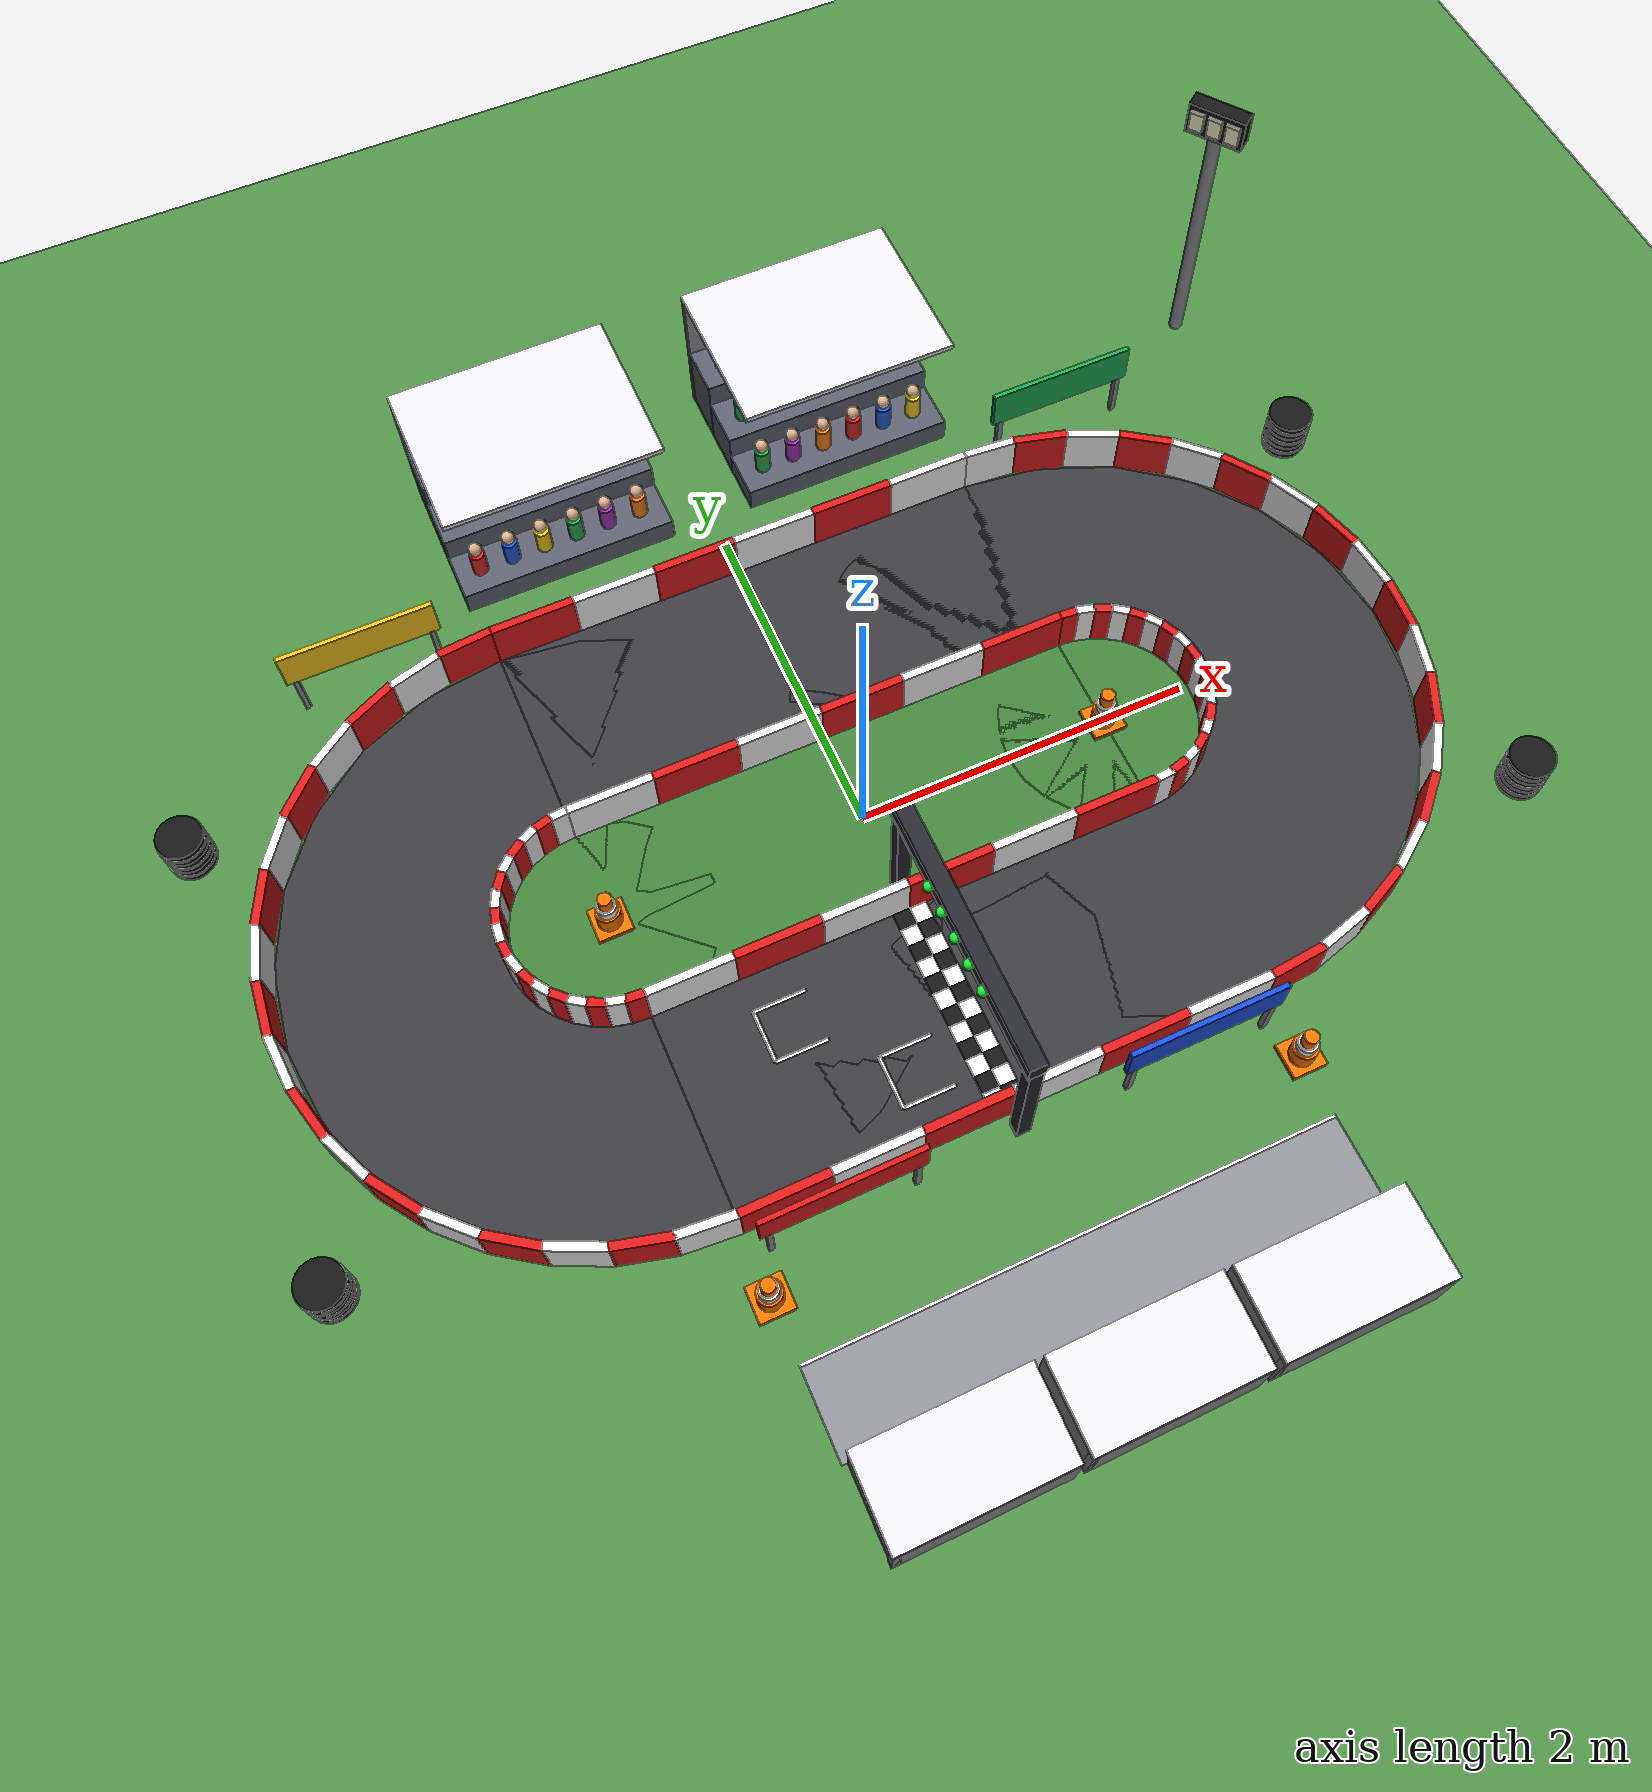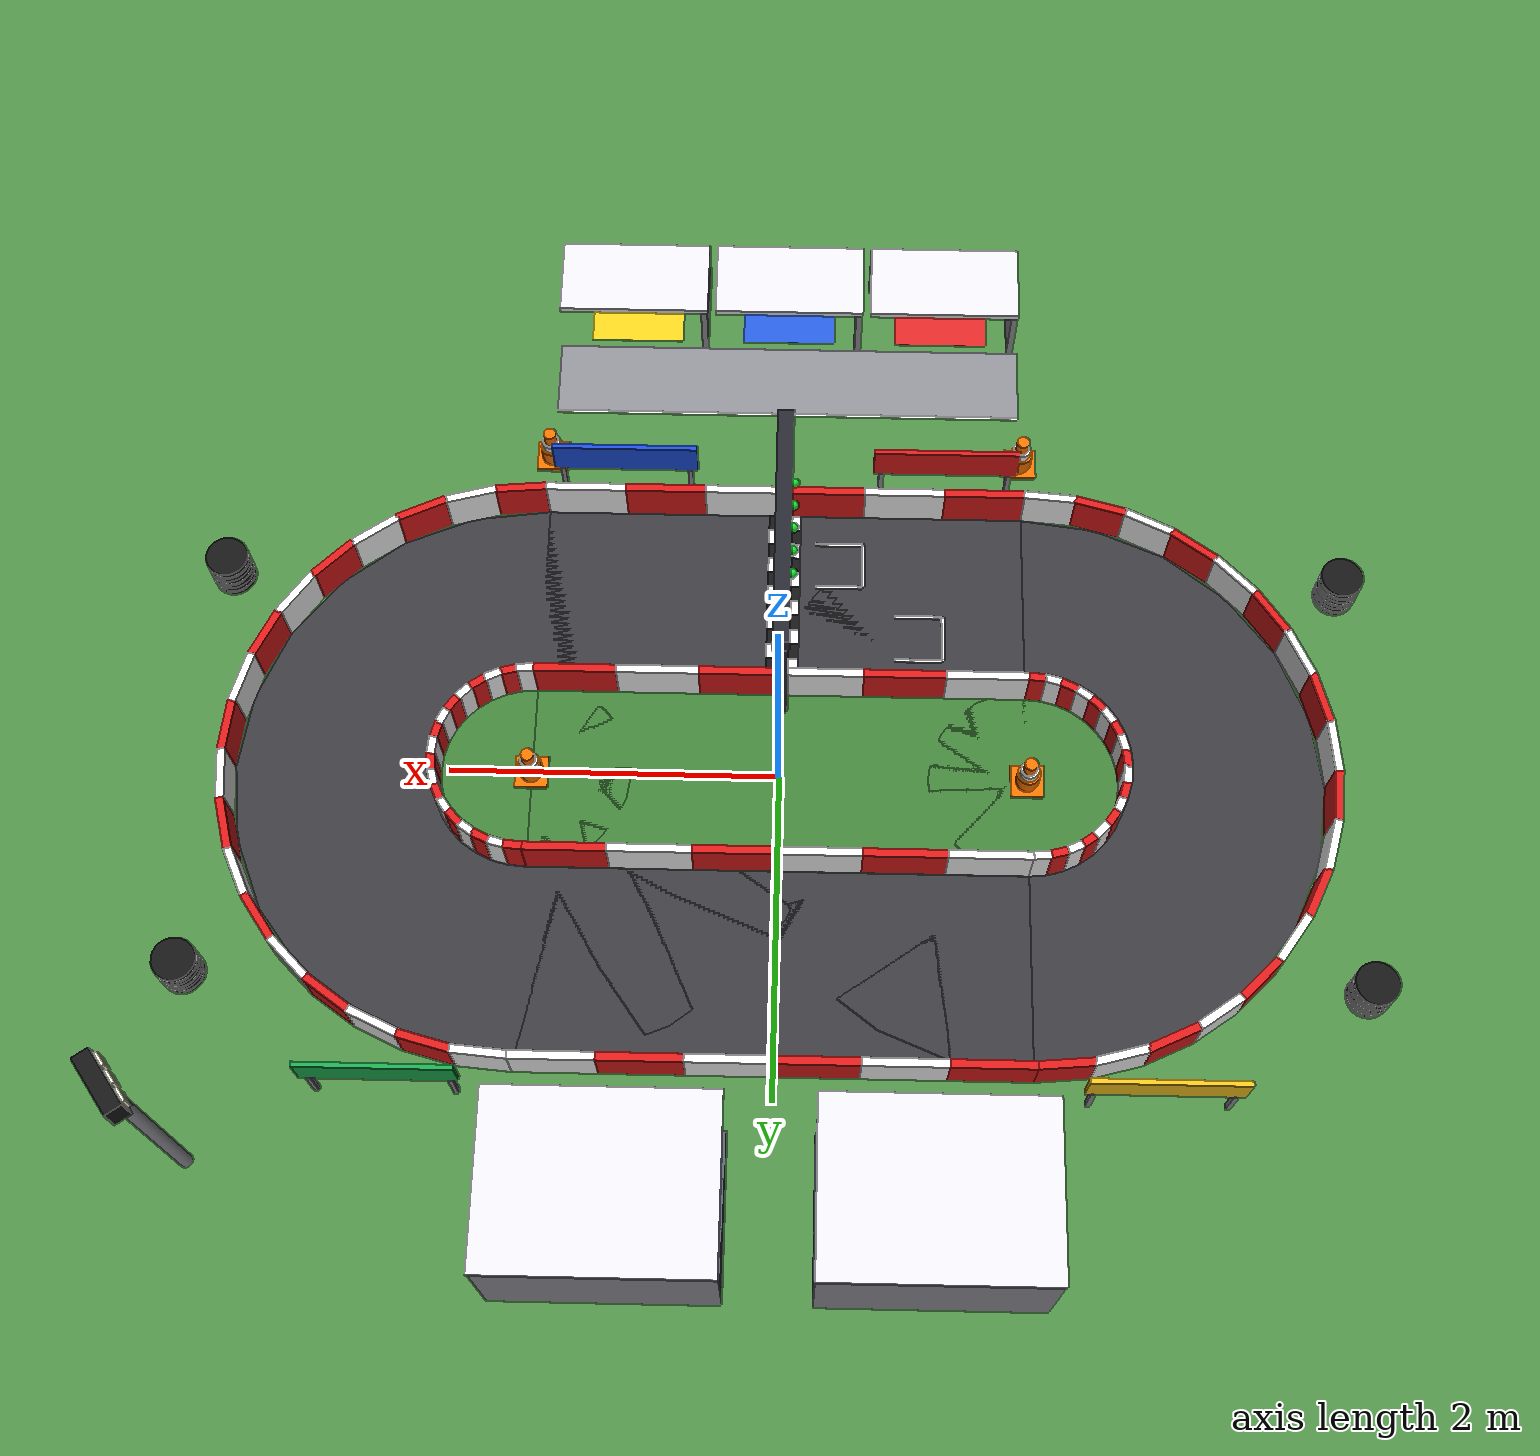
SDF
<?xml version="1.0"?>
<!-- Generated by world_gen/generate_world.py from config/circuit.yaml. Do not edit by hand. -->
<sdf version="1.6">
<world name="apex_circuit">
<physics type="ode">
  <real_time_update_rate>1000.0</real_time_update_rate>
  <max_step_size>0.001</max_step_size>
  <real_time_factor>1</real_time_factor>
</physics>
<scene>
  <ambient>0.55 0.55 0.55 1</ambient>
  <background>0.7 0.82 0.95 1</background>
  <shadows>false</shadows>
</scene>
<gui fullscreen="0">
  <camera name="user_camera">
    <pose>0 -6.5 5.5 0 0.72 1.5708</pose>
  </camera>
</gui>
<light name="sun" type="directional">
  <cast_shadows>false</cast_shadows>
  <pose>0 0 10 0 0 0</pose>
  <diffuse>0.85 0.85 0.85 1</diffuse>
  <specular>0.2 0.2 0.2 1</specular>
  <direction>-0.4 0.3 -0.9</direction>
</light>
<plugin name="gazebo_ros_state" filename="libgazebo_ros_state.so">
  <ros><namespace>/gazebo</namespace></ros>
  <update_rate>10.0</update_rate>
</plugin>
<model name="ground_plane">
  <static>true</static>
  <link name="link">
    <collision name="collision">
      <geometry><plane><normal>0 0 1</normal><size>40 40</size></plane></geometry>
      <surface><friction><ode><mu>100</mu><mu2>50</mu2></ode></friction></surface>
    </collision>
    <visual name="visual">
      <geometry><plane><normal>0 0 1</normal><size>40 40</size></plane></geometry>
      <material><ambient>0.3 0.55 0.27 1</ambient><diffuse>0.3 0.55 0.27 1</diffuse></material>
    </visual>
  </link>
</model>

<model name="track_surface"><static>true</static><pose>0.0000 0.0000 0 0 0 0.0000</pose><link name="link">
<visual name="asphalt_mid_v"><pose>0.0000 0.0000 0.0010 0 0 0.0000</pose><geometry><box><size>3.0000 3.6000 0.0020</size></box></geometry><material><ambient>0.22 0.22 0.24 1</ambient><diffuse>0.22 0.22 0.24 1</diffuse></material></visual>
<visual name="asphalt_e_v"><pose>1.5000 0.0000 0.0010 0 0 0.0000</pose><geometry><cylinder><radius>1.8000</radius><length>0.0020</length></cylinder></geometry><material><ambient>0.22 0.22 0.24 1</ambient><diffuse>0.22 0.22 0.24 1</diffuse></material></visual>
<visual name="asphalt_w_v"><pose>-1.5000 0.0000 0.0010 0 0 0.0000</pose><geometry><cylinder><radius>1.8000</radius><length>0.0020</length></cylinder></geometry><material><ambient>0.22 0.22 0.24 1</ambient><diffuse>0.22 0.22 0.24 1</diffuse></material></visual>
<visual name="infield_mid_v"><pose>0.0000 0.0000 0.0030 0 0 0.0000</pose><geometry><box><size>3.0000 1.2000 0.0020</size></box></geometry><material><ambient>0.25 0.5 0.22 1</ambient><diffuse>0.25 0.5 0.22 1</diffuse></material></visual>
<visual name="infield_e_v"><pose>1.5000 0.0000 0.0030 0 0 0.0000</pose><geometry><cylinder><radius>0.6000</radius><length>0.0020</length></cylinder></geometry><material><ambient>0.25 0.5 0.22 1</ambient><diffuse>0.25 0.5 0.22 1</diffuse></material></visual>
<visual name="infield_w_v"><pose>-1.5000 0.0000 0.0030 0 0 0.0000</pose><geometry><cylinder><radius>0.6000</radius><length>0.0020</length></cylinder></geometry><material><ambient>0.25 0.5 0.22 1</ambient><diffuse>0.25 0.5 0.22 1</diffuse></material></visual>
<visual name="line_0_0_v"><pose>-0.0500 -1.7500 0.0040 0 0 0.0000</pose><geometry><box><size>0.1000 0.1000 0.0020</size></box></geometry><material><ambient>0.95 0.95 0.95 1</ambient><diffuse>0.95 0.95 0.95 1</diffuse></material></visual>
<visual name="line_0_1_v"><pose>0.0500 -1.7500 0.0040 0 0 0.0000</pose><geometry><box><size>0.1000 0.1000 0.0020</size></box></geometry><material><ambient>0.08 0.08 0.08 1</ambient><diffuse>0.08 0.08 0.08 1</diffuse></material></visual>
<visual name="line_1_0_v"><pose>-0.0500 -1.6500 0.0040 0 0 0.0000</pose><geometry><box><size>0.1000 0.1000 0.0020</size></box></geometry><material><ambient>0.08 0.08 0.08 1</ambient><diffuse>0.08 0.08 0.08 1</diffuse></material></visual>
<visual name="line_1_1_v"><pose>0.0500 -1.6500 0.0040 0 0 0.0000</pose><geometry><box><size>0.1000 0.1000 0.0020</size></box></geometry><material><ambient>0.95 0.95 0.95 1</ambient><diffuse>0.95 0.95 0.95 1</diffuse></material></visual>
<visual name="line_2_0_v"><pose>-0.0500 -1.5500 0.0040 0 0 0.0000</pose><geometry><box><size>0.1000 0.1000 0.0020</size></box></geometry><material><ambient>0.95 0.95 0.95 1</ambient><diffuse>0.95 0.95 0.95 1</diffuse></material></visual>
<visual name="line_2_1_v"><pose>0.0500 -1.5500 0.0040 0 0 0.0000</pose><geometry><box><size>0.1000 0.1000 0.0020</size></box></geometry><material><ambient>0.08 0.08 0.08 1</ambient><diffuse>0.08 0.08 0.08 1</diffuse></material></visual>
<visual name="line_3_0_v"><pose>-0.0500 -1.4500 0.0040 0 0 0.0000</pose><geometry><box><size>0.1000 0.1000 0.0020</size></box></geometry><material><ambient>0.08 0.08 0.08 1</ambient><diffuse>0.08 0.08 0.08 1</diffuse></material></visual>
<visual name="line_3_1_v"><pose>0.0500 -1.4500 0.0040 0 0 0.0000</pose><geometry><box><size>0.1000 0.1000 0.0020</size></box></geometry><material><ambient>0.95 0.95 0.95 1</ambient><diffuse>0.95 0.95 0.95 1</diffuse></material></visual>
<visual name="line_4_0_v"><pose>-0.0500 -1.3500 0.0040 0 0 0.0000</pose><geometry><box><size>0.1000 0.1000 0.0020</size></box></geometry><material><ambient>0.95 0.95 0.95 1</ambient><diffuse>0.95 0.95 0.95 1</diffuse></material></visual>
<visual name="line_4_1_v"><pose>0.0500 -1.3500 0.0040 0 0 0.0000</pose><geometry><box><size>0.1000 0.1000 0.0020</size></box></geometry><material><ambient>0.08 0.08 0.08 1</ambient><diffuse>0.08 0.08 0.08 1</diffuse></material></visual>
<visual name="line_5_0_v"><pose>-0.0500 -1.2500 0.0040 0 0 0.0000</pose><geometry><box><size>0.1000 0.1000 0.0020</size></box></geometry><material><ambient>0.08 0.08 0.08 1</ambient><diffuse>0.08 0.08 0.08 1</diffuse></material></visual>
<visual name="line_5_1_v"><pose>0.0500 -1.2500 0.0040 0 0 0.0000</pose><geometry><box><size>0.1000 0.1000 0.0020</size></box></geometry><material><ambient>0.95 0.95 0.95 1</ambient><diffuse>0.95 0.95 0.95 1</diffuse></material></visual>
<visual name="line_6_0_v"><pose>-0.0500 -1.1500 0.0040 0 0 0.0000</pose><geometry><box><size>0.1000 0.1000 0.0020</size></box></geometry><material><ambient>0.95 0.95 0.95 1</ambient><diffuse>0.95 0.95 0.95 1</diffuse></material></visual>
<visual name="line_6_1_v"><pose>0.0500 -1.1500 0.0040 0 0 0.0000</pose><geometry><box><size>0.1000 0.1000 0.0020</size></box></geometry><material><ambient>0.08 0.08 0.08 1</ambient><diffuse>0.08 0.08 0.08 1</diffuse></material></visual>
<visual name="line_7_0_v"><pose>-0.0500 -1.0500 0.0040 0 0 0.0000</pose><geometry><box><size>0.1000 0.1000 0.0020</size></box></geometry><material><ambient>0.08 0.08 0.08 1</ambient><diffuse>0.08 0.08 0.08 1</diffuse></material></visual>
<visual name="line_7_1_v"><pose>0.0500 -1.0500 0.0040 0 0 0.0000</pose><geometry><box><size>0.1000 0.1000 0.0020</size></box></geometry><material><ambient>0.95 0.95 0.95 1</ambient><diffuse>0.95 0.95 0.95 1</diffuse></material></visual>
<visual name="line_8_0_v"><pose>-0.0500 -0.9500 0.0040 0 0 0.0000</pose><geometry><box><size>0.1000 0.1000 0.0020</size></box></geometry><material><ambient>0.95 0.95 0.95 1</ambient><diffuse>0.95 0.95 0.95 1</diffuse></material></visual>
<visual name="line_8_1_v"><pose>0.0500 -0.9500 0.0040 0 0 0.0000</pose><geometry><box><size>0.1000 0.1000 0.0020</size></box></geometry><material><ambient>0.08 0.08 0.08 1</ambient><diffuse>0.08 0.08 0.08 1</diffuse></material></visual>
<visual name="line_9_0_v"><pose>-0.0500 -0.8500 0.0040 0 0 0.0000</pose><geometry><box><size>0.1000 0.1000 0.0020</size></box></geometry><material><ambient>0.08 0.08 0.08 1</ambient><diffuse>0.08 0.08 0.08 1</diffuse></material></visual>
<visual name="line_9_1_v"><pose>0.0500 -0.8500 0.0040 0 0 0.0000</pose><geometry><box><size>0.1000 0.1000 0.0020</size></box></geometry><material><ambient>0.95 0.95 0.95 1</ambient><diffuse>0.95 0.95 0.95 1</diffuse></material></visual>
<visual name="line_10_0_v"><pose>-0.0500 -0.7500 0.0040 0 0 0.0000</pose><geometry><box><size>0.1000 0.1000 0.0020</size></box></geometry><material><ambient>0.95 0.95 0.95 1</ambient><diffuse>0.95 0.95 0.95 1</diffuse></material></visual>
<visual name="line_10_1_v"><pose>0.0500 -0.7500 0.0040 0 0 0.0000</pose><geometry><box><size>0.1000 0.1000 0.0020</size></box></geometry><material><ambient>0.08 0.08 0.08 1</ambient><diffuse>0.08 0.08 0.08 1</diffuse></material></visual>
<visual name="line_11_0_v"><pose>-0.0500 -0.6500 0.0040 0 0 0.0000</pose><geometry><box><size>0.1000 0.1000 0.0020</size></box></geometry><material><ambient>0.08 0.08 0.08 1</ambient><diffuse>0.08 0.08 0.08 1</diffuse></material></visual>
<visual name="line_11_1_v"><pose>0.0500 -0.6500 0.0040 0 0 0.0000</pose><geometry><box><size>0.1000 0.1000 0.0020</size></box></geometry><material><ambient>0.95 0.95 0.95 1</ambient><diffuse>0.95 0.95 0.95 1</diffuse></material></visual>
<visual name="grid_auto_back_v"><pose>-0.5000 -1.4500 0.0040 0 0 0.0000</pose><geometry><box><size>0.0200 0.3000 0.0020</size></box></geometry><material><ambient>0.95 0.95 0.95 1</ambient><diffuse>0.95 0.95 0.95 1</diffuse></material></visual>
<visual name="grid_auto_-1_v"><pose>-0.3500 -1.6000 0.0040 0 0 0.0000</pose><geometry><box><size>0.3000 0.0200 0.0020</size></box></geometry><material><ambient>0.95 0.95 0.95 1</ambient><diffuse>0.95 0.95 0.95 1</diffuse></material></visual>
<visual name="grid_auto_1_v"><pose>-0.3500 -1.3000 0.0040 0 0 0.0000</pose><geometry><box><size>0.3000 0.0200 0.0020</size></box></geometry><material><ambient>0.95 0.95 0.95 1</ambient><diffuse>0.95 0.95 0.95 1</diffuse></material></visual>
<visual name="grid_player_back_v"><pose>-1.0000 -0.9500 0.0040 0 0 0.0000</pose><geometry><box><size>0.0200 0.3000 0.0020</size></box></geometry><material><ambient>0.95 0.95 0.95 1</ambient><diffuse>0.95 0.95 0.95 1</diffuse></material></visual>
<visual name="grid_player_-1_v"><pose>-0.8500 -1.1000 0.0040 0 0 0.0000</pose><geometry><box><size>0.3000 0.0200 0.0020</size></box></geometry><material><ambient>0.95 0.95 0.95 1</ambient><diffuse>0.95 0.95 0.95 1</diffuse></material></visual>
<visual name="grid_player_1_v"><pose>-0.8500 -0.8000 0.0040 0 0 0.0000</pose><geometry><box><size>0.3000 0.0200 0.0020</size></box></geometry><material><ambient>0.95 0.95 0.95 1</ambient><diffuse>0.95 0.95 0.95 1</diffuse></material></visual>
</link></model>

<model name="barrier_walls"><static>true</static><pose>0.0000 0.0000 0 0 0 0.0000</pose><link name="link">
<visual name="outer0_v"><pose>-1.2500 -1.8250 0.1500 0 0 0.0000</pose><geometry><box><size>0.5000 0.0500 0.3000</size></box></geometry><material><ambient>0.85 0.1 0.1 1</ambient><diffuse>0.85 0.1 0.1 1</diffuse></material></visual><collision name="outer0_c"><pose>-1.2500 -1.8250 0.1500 0 0 0.0000</pose><geometry><box><size>0.5000 0.0500 0.3000</size></box></geometry></collision>
<visual name="outer1_v"><pose>-0.7500 -1.8250 0.1500 0 0 0.0000</pose><geometry><box><size>0.5000 0.0500 0.3000</size></box></geometry><material><ambient>0.95 0.95 0.95 1</ambient><diffuse>0.95 0.95 0.95 1</diffuse></material></visual><collision name="outer1_c"><pose>-0.7500 -1.8250 0.1500 0 0 0.0000</pose><geometry><box><size>0.5000 0.0500 0.3000</size></box></geometry></collision>
<visual name="outer2_v"><pose>-0.2500 -1.8250 0.1500 0 0 0.0000</pose><geometry><box><size>0.5000 0.0500 0.3000</size></box></geometry><material><ambient>0.85 0.1 0.1 1</ambient><diffuse>0.85 0.1 0.1 1</diffuse></material></visual><collision name="outer2_c"><pose>-0.2500 -1.8250 0.1500 0 0 0.0000</pose><geometry><box><size>0.5000 0.0500 0.3000</size></box></geometry></collision>
<visual name="outer3_v"><pose>0.2500 -1.8250 0.1500 0 0 0.0000</pose><geometry><box><size>0.5000 0.0500 0.3000</size></box></geometry><material><ambient>0.95 0.95 0.95 1</ambient><diffuse>0.95 0.95 0.95 1</diffuse></material></visual><collision name="outer3_c"><pose>0.2500 -1.8250 0.1500 0 0 0.0000</pose><geometry><box><size>0.5000 0.0500 0.3000</size></box></geometry></collision>
<visual name="outer4_v"><pose>0.7500 -1.8250 0.1500 0 0 0.0000</pose><geometry><box><size>0.5000 0.0500 0.3000</size></box></geometry><material><ambient>0.85 0.1 0.1 1</ambient><diffuse>0.85 0.1 0.1 1</diffuse></material></visual><collision name="outer4_c"><pose>0.7500 -1.8250 0.1500 0 0 0.0000</pose><geometry><box><size>0.5000 0.0500 0.3000</size></box></geometry></collision>
<visual name="outer5_v"><pose>1.2500 -1.8250 0.1500 0 0 0.0000</pose><geometry><box><size>0.5000 0.0500 0.3000</size></box></geometry><material><ambient>0.95 0.95 0.95 1</ambient><diffuse>0.95 0.95 0.95 1</diffuse></material></visual><collision name="outer5_c"><pose>1.2500 -1.8250 0.1500 0 0 0.0000</pose><geometry><box><size>0.5000 0.0500 0.3000</size></box></geometry></collision>
<visual name="outer6_v"><pose>-1.2500 1.8250 0.1500 0 0 0.0000</pose><geometry><box><size>0.5000 0.0500 0.3000</size></box></geometry><material><ambient>0.85 0.1 0.1 1</ambient><diffuse>0.85 0.1 0.1 1</diffuse></material></visual><collision name="outer6_c"><pose>-1.2500 1.8250 0.1500 0 0 0.0000</pose><geometry><box><size>0.5000 0.0500 0.3000</size></box></geometry></collision>
<visual name="outer7_v"><pose>-0.7500 1.8250 0.1500 0 0 0.0000</pose><geometry><box><size>0.5000 0.0500 0.3000</size></box></geometry><material><ambient>0.95 0.95 0.95 1</ambient><diffuse>0.95 0.95 0.95 1</diffuse></material></visual><collision name="outer7_c"><pose>-0.7500 1.8250 0.1500 0 0 0.0000</pose><geometry><box><size>0.5000 0.0500 0.3000</size></box></geometry></collision>
<visual name="outer8_v"><pose>-0.2500 1.8250 0.1500 0 0 0.0000</pose><geometry><box><size>0.5000 0.0500 0.3000</size></box></geometry><material><ambient>0.85 0.1 0.1 1</ambient><diffuse>0.85 0.1 0.1 1</diffuse></material></visual><collision name="outer8_c"><pose>-0.2500 1.8250 0.1500 0 0 0.0000</pose><geometry><box><size>0.5000 0.0500 0.3000</size></box></geometry></collision>
<visual name="outer9_v"><pose>0.2500 1.8250 0.1500 0 0 0.0000</pose><geometry><box><size>0.5000 0.0500 0.3000</size></box></geometry><material><ambient>0.95 0.95 0.95 1</ambient><diffuse>0.95 0.95 0.95 1</diffuse></material></visual><collision name="outer9_c"><pose>0.2500 1.8250 0.1500 0 0 0.0000</pose><geometry><box><size>0.5000 0.0500 0.3000</size></box></geometry></collision>
<visual name="outer10_v"><pose>0.7500 1.8250 0.1500 0 0 0.0000</pose><geometry><box><size>0.5000 0.0500 0.3000</size></box></geometry><material><ambient>0.85 0.1 0.1 1</ambient><diffuse>0.85 0.1 0.1 1</diffuse></material></visual><collision name="outer10_c"><pose>0.7500 1.8250 0.1500 0 0 0.0000</pose><geometry><box><size>0.5000 0.0500 0.3000</size></box></geometry></collision>
<visual name="outer11_v"><pose>1.2500 1.8250 0.1500 0 0 0.0000</pose><geometry><box><size>0.5000 0.0500 0.3000</size></box></geometry><material><ambient>0.95 0.95 0.95 1</ambient><diffuse>0.95 0.95 0.95 1</diffuse></material></visual><collision name="outer11_c"><pose>1.2500 1.8250 0.1500 0 0 0.0000</pose><geometry><box><size>0.5000 0.0500 0.3000</size></box></geometry></collision>
<visual name="outer12_v"><pose>1.6585 -1.8111 0.1500 0 0 0.0873</pose><geometry><box><size>0.3281 0.0500 0.3000</size></box></geometry><material><ambient>0.85 0.1 0.1 1</ambient><diffuse>0.85 0.1 0.1 1</diffuse></material></visual><collision name="outer12_c"><pose>1.6585 -1.8111 0.1500 0 0 0.0873</pose><geometry><box><size>0.3281 0.0500 0.3000</size></box></geometry></collision>
<visual name="outer13_v"><pose>1.9705 -1.7561 0.1500 0 0 0.2618</pose><geometry><box><size>0.3281 0.0500 0.3000</size></box></geometry><material><ambient>0.95 0.95 0.95 1</ambient><diffuse>0.95 0.95 0.95 1</diffuse></material></visual><collision name="outer13_c"><pose>1.9705 -1.7561 0.1500 0 0 0.2618</pose><geometry><box><size>0.3281 0.0500 0.3000</size></box></geometry></collision>
<visual name="outer14_v"><pose>2.2683 -1.6477 0.1500 0 0 0.4363</pose><geometry><box><size>0.3281 0.0500 0.3000</size></box></geometry><material><ambient>0.85 0.1 0.1 1</ambient><diffuse>0.85 0.1 0.1 1</diffuse></material></visual><collision name="outer14_c"><pose>2.2683 -1.6477 0.1500 0 0 0.4363</pose><geometry><box><size>0.3281 0.0500 0.3000</size></box></geometry></collision>
<visual name="outer15_v"><pose>2.5428 -1.4893 0.1500 0 0 0.6109</pose><geometry><box><size>0.3281 0.0500 0.3000</size></box></geometry><material><ambient>0.95 0.95 0.95 1</ambient><diffuse>0.95 0.95 0.95 1</diffuse></material></visual><collision name="outer15_c"><pose>2.5428 -1.4893 0.1500 0 0 0.6109</pose><geometry><box><size>0.3281 0.0500 0.3000</size></box></geometry></collision>
<visual name="outer16_v"><pose>2.7856 -1.2856 0.1500 0 0 0.7854</pose><geometry><box><size>0.3281 0.0500 0.3000</size></box></geometry><material><ambient>0.85 0.1 0.1 1</ambient><diffuse>0.85 0.1 0.1 1</diffuse></material></visual><collision name="outer16_c"><pose>2.7856 -1.2856 0.1500 0 0 0.7854</pose><geometry><box><size>0.3281 0.0500 0.3000</size></box></geometry></collision>
<visual name="outer17_v"><pose>2.9893 -1.0428 0.1500 0 0 0.9599</pose><geometry><box><size>0.3281 0.0500 0.3000</size></box></geometry><material><ambient>0.95 0.95 0.95 1</ambient><diffuse>0.95 0.95 0.95 1</diffuse></material></visual><collision name="outer17_c"><pose>2.9893 -1.0428 0.1500 0 0 0.9599</pose><geometry><box><size>0.3281 0.0500 0.3000</size></box></geometry></collision>
<visual name="outer18_v"><pose>3.1477 -0.7683 0.1500 0 0 1.1345</pose><geometry><box><size>0.3281 0.0500 0.3000</size></box></geometry><material><ambient>0.85 0.1 0.1 1</ambient><diffuse>0.85 0.1 0.1 1</diffuse></material></visual><collision name="outer18_c"><pose>3.1477 -0.7683 0.1500 0 0 1.1345</pose><geometry><box><size>0.3281 0.0500 0.3000</size></box></geometry></collision>
<visual name="outer19_v"><pose>3.2561 -0.4705 0.1500 0 0 1.3090</pose><geometry><box><size>0.3281 0.0500 0.3000</size></box></geometry><material><ambient>0.95 0.95 0.95 1</ambient><diffuse>0.95 0.95 0.95 1</diffuse></material></visual><collision name="outer19_c"><pose>3.2561 -0.4705 0.1500 0 0 1.3090</pose><geometry><box><size>0.3281 0.0500 0.3000</size></box></geometry></collision>
<visual name="outer20_v"><pose>3.3111 -0.1585 0.1500 0 0 1.4835</pose><geometry><box><size>0.3281 0.0500 0.3000</size></box></geometry><material><ambient>0.85 0.1 0.1 1</ambient><diffuse>0.85 0.1 0.1 1</diffuse></material></visual><collision name="outer20_c"><pose>3.3111 -0.1585 0.1500 0 0 1.4835</pose><geometry><box><size>0.3281 0.0500 0.3000</size></box></geometry></collision>
<visual name="outer21_v"><pose>3.3111 0.1585 0.1500 0 0 1.6581</pose><geometry><box><size>0.3281 0.0500 0.3000</size></box></geometry><material><ambient>0.95 0.95 0.95 1</ambient><diffuse>0.95 0.95 0.95 1</diffuse></material></visual><collision name="outer21_c"><pose>3.3111 0.1585 0.1500 0 0 1.6581</pose><geometry><box><size>0.3281 0.0500 0.3000</size></box></geometry></collision>
<visual name="outer22_v"><pose>3.2561 0.4705 0.1500 0 0 1.8326</pose><geometry><box><size>0.3281 0.0500 0.3000</size></box></geometry><material><ambient>0.85 0.1 0.1 1</ambient><diffuse>0.85 0.1 0.1 1</diffuse></material></visual><collision name="outer22_c"><pose>3.2561 0.4705 0.1500 0 0 1.8326</pose><geometry><box><size>0.3281 0.0500 0.3000</size></box></geometry></collision>
<visual name="outer23_v"><pose>3.1477 0.7683 0.1500 0 0 2.0071</pose><geometry><box><size>0.3281 0.0500 0.3000</size></box></geometry><material><ambient>0.95 0.95 0.95 1</ambient><diffuse>0.95 0.95 0.95 1</diffuse></material></visual><collision name="outer23_c"><pose>3.1477 0.7683 0.1500 0 0 2.0071</pose><geometry><box><size>0.3281 0.0500 0.3000</size></box></geometry></collision>
<visual name="outer24_v"><pose>2.9893 1.0428 0.1500 0 0 2.1817</pose><geometry><box><size>0.3281 0.0500 0.3000</size></box></geometry><material><ambient>0.85 0.1 0.1 1</ambient><diffuse>0.85 0.1 0.1 1</diffuse></material></visual><collision name="outer24_c"><pose>2.9893 1.0428 0.1500 0 0 2.1817</pose><geometry><box><size>0.3281 0.0500 0.3000</size></box></geometry></collision>
<visual name="outer25_v"><pose>2.7856 1.2856 0.1500 0 0 2.3562</pose><geometry><box><size>0.3281 0.0500 0.3000</size></box></geometry><material><ambient>0.95 0.95 0.95 1</ambient><diffuse>0.95 0.95 0.95 1</diffuse></material></visual><collision name="outer25_c"><pose>2.7856 1.2856 0.1500 0 0 2.3562</pose><geometry><box><size>0.3281 0.0500 0.3000</size></box></geometry></collision>
<visual name="outer26_v"><pose>2.5428 1.4893 0.1500 0 0 2.5307</pose><geometry><box><size>0.3281 0.0500 0.3000</size></box></geometry><material><ambient>0.85 0.1 0.1 1</ambient><diffuse>0.85 0.1 0.1 1</diffuse></material></visual><collision name="outer26_c"><pose>2.5428 1.4893 0.1500 0 0 2.5307</pose><geometry><box><size>0.3281 0.0500 0.3000</size></box></geometry></collision>
<visual name="outer27_v"><pose>2.2683 1.6477 0.1500 0 0 2.7053</pose><geometry><box><size>0.3281 0.0500 0.3000</size></box></geometry><material><ambient>0.95 0.95 0.95 1</ambient><diffuse>0.95 0.95 0.95 1</diffuse></material></visual><collision name="outer27_c"><pose>2.2683 1.6477 0.1500 0 0 2.7053</pose><geometry><box><size>0.3281 0.0500 0.3000</size></box></geometry></collision>
<visual name="outer28_v"><pose>1.9705 1.7561 0.1500 0 0 2.8798</pose><geometry><box><size>0.3281 0.0500 0.3000</size></box></geometry><material><ambient>0.85 0.1 0.1 1</ambient><diffuse>0.85 0.1 0.1 1</diffuse></material></visual><collision name="outer28_c"><pose>1.9705 1.7561 0.1500 0 0 2.8798</pose><geometry><box><size>0.3281 0.0500 0.3000</size></box></geometry></collision>
<visual name="outer29_v"><pose>1.6585 1.8111 0.1500 0 0 3.0543</pose><geometry><box><size>0.3281 0.0500 0.3000</size></box></geometry><material><ambient>0.95 0.95 0.95 1</ambient><diffuse>0.95 0.95 0.95 1</diffuse></material></visual><collision name="outer29_c"><pose>1.6585 1.8111 0.1500 0 0 3.0543</pose><geometry><box><size>0.3281 0.0500 0.3000</size></box></geometry></collision>
<visual name="outer30_v"><pose>-1.6585 1.8111 0.1500 0 0 3.2289</pose><geometry><box><size>0.3281 0.0500 0.3000</size></box></geometry><material><ambient>0.85 0.1 0.1 1</ambient><diffuse>0.85 0.1 0.1 1</diffuse></material></visual><collision name="outer30_c"><pose>-1.6585 1.8111 0.1500 0 0 3.2289</pose><geometry><box><size>0.3281 0.0500 0.3000</size></box></geometry></collision>
<visual name="outer31_v"><pose>-1.9705 1.7561 0.1500 0 0 3.4034</pose><geometry><box><size>0.3281 0.0500 0.3000</size></box></geometry><material><ambient>0.95 0.95 0.95 1</ambient><diffuse>0.95 0.95 0.95 1</diffuse></material></visual><collision name="outer31_c"><pose>-1.9705 1.7561 0.1500 0 0 3.4034</pose><geometry><box><size>0.3281 0.0500 0.3000</size></box></geometry></collision>
<visual name="outer32_v"><pose>-2.2683 1.6477 0.1500 0 0 3.5779</pose><geometry><box><size>0.3281 0.0500 0.3000</size></box></geometry><material><ambient>0.85 0.1 0.1 1</ambient><diffuse>0.85 0.1 0.1 1</diffuse></material></visual><collision name="outer32_c"><pose>-2.2683 1.6477 0.1500 0 0 3.5779</pose><geometry><box><size>0.3281 0.0500 0.3000</size></box></geometry></collision>
<visual name="outer33_v"><pose>-2.5428 1.4893 0.1500 0 0 3.7525</pose><geometry><box><size>0.3281 0.0500 0.3000</size></box></geometry><material><ambient>0.95 0.95 0.95 1</ambient><diffuse>0.95 0.95 0.95 1</diffuse></material></visual><collision name="outer33_c"><pose>-2.5428 1.4893 0.1500 0 0 3.7525</pose><geometry><box><size>0.3281 0.0500 0.3000</size></box></geometry></collision>
<visual name="outer34_v"><pose>-2.7856 1.2856 0.1500 0 0 3.9270</pose><geometry><box><size>0.3281 0.0500 0.3000</size></box></geometry><material><ambient>0.85 0.1 0.1 1</ambient><diffuse>0.85 0.1 0.1 1</diffuse></material></visual><collision name="outer34_c"><pose>-2.7856 1.2856 0.1500 0 0 3.9270</pose><geometry><box><size>0.3281 0.0500 0.3000</size></box></geometry></collision>
<visual name="outer35_v"><pose>-2.9893 1.0428 0.1500 0 0 4.1015</pose><geometry><box><size>0.3281 0.0500 0.3000</size></box></geometry><material><ambient>0.95 0.95 0.95 1</ambient><diffuse>0.95 0.95 0.95 1</diffuse></material></visual><collision name="outer35_c"><pose>-2.9893 1.0428 0.1500 0 0 4.1015</pose><geometry><box><size>0.3281 0.0500 0.3000</size></box></geometry></collision>
<visual name="outer36_v"><pose>-3.1477 0.7683 0.1500 0 0 4.2761</pose><geometry><box><size>0.3281 0.0500 0.3000</size></box></geometry><material><ambient>0.85 0.1 0.1 1</ambient><diffuse>0.85 0.1 0.1 1</diffuse></material></visual><collision name="outer36_c"><pose>-3.1477 0.7683 0.1500 0 0 4.2761</pose><geometry><box><size>0.3281 0.0500 0.3000</size></box></geometry></collision>
<visual name="outer37_v"><pose>-3.2561 0.4705 0.1500 0 0 4.4506</pose><geometry><box><size>0.3281 0.0500 0.3000</size></box></geometry><material><ambient>0.95 0.95 0.95 1</ambient><diffuse>0.95 0.95 0.95 1</diffuse></material></visual><collision name="outer37_c"><pose>-3.2561 0.4705 0.1500 0 0 4.4506</pose><geometry><box><size>0.3281 0.0500 0.3000</size></box></geometry></collision>
<visual name="outer38_v"><pose>-3.3111 0.1585 0.1500 0 0 4.6251</pose><geometry><box><size>0.3281 0.0500 0.3000</size></box></geometry><material><ambient>0.85 0.1 0.1 1</ambient><diffuse>0.85 0.1 0.1 1</diffuse></material></visual><collision name="outer38_c"><pose>-3.3111 0.1585 0.1500 0 0 4.6251</pose><geometry><box><size>0.3281 0.0500 0.3000</size></box></geometry></collision>
<visual name="outer39_v"><pose>-3.3111 -0.1585 0.1500 0 0 4.7997</pose><geometry><box><size>0.3281 0.0500 0.3000</size></box></geometry><material><ambient>0.95 0.95 0.95 1</ambient><diffuse>0.95 0.95 0.95 1</diffuse></material></visual><collision name="outer39_c"><pose>-3.3111 -0.1585 0.1500 0 0 4.7997</pose><geometry><box><size>0.3281 0.0500 0.3000</size></box></geometry></collision>
<visual name="outer40_v"><pose>-3.2561 -0.4705 0.1500 0 0 4.9742</pose><geometry><box><size>0.3281 0.0500 0.3000</size></box></geometry><material><ambient>0.85 0.1 0.1 1</ambient><diffuse>0.85 0.1 0.1 1</diffuse></material></visual><collision name="outer40_c"><pose>-3.2561 -0.4705 0.1500 0 0 4.9742</pose><geometry><box><size>0.3281 0.0500 0.3000</size></box></geometry></collision>
<visual name="outer41_v"><pose>-3.1477 -0.7683 0.1500 0 0 5.1487</pose><geometry><box><size>0.3281 0.0500 0.3000</size></box></geometry><material><ambient>0.95 0.95 0.95 1</ambient><diffuse>0.95 0.95 0.95 1</diffuse></material></visual><collision name="outer41_c"><pose>-3.1477 -0.7683 0.1500 0 0 5.1487</pose><geometry><box><size>0.3281 0.0500 0.3000</size></box></geometry></collision>
<visual name="outer42_v"><pose>-2.9893 -1.0428 0.1500 0 0 5.3233</pose><geometry><box><size>0.3281 0.0500 0.3000</size></box></geometry><material><ambient>0.85 0.1 0.1 1</ambient><diffuse>0.85 0.1 0.1 1</diffuse></material></visual><collision name="outer42_c"><pose>-2.9893 -1.0428 0.1500 0 0 5.3233</pose><geometry><box><size>0.3281 0.0500 0.3000</size></box></geometry></collision>
<visual name="outer43_v"><pose>-2.7856 -1.2856 0.1500 0 0 5.4978</pose><geometry><box><size>0.3281 0.0500 0.3000</size></box></geometry><material><ambient>0.95 0.95 0.95 1</ambient><diffuse>0.95 0.95 0.95 1</diffuse></material></visual><collision name="outer43_c"><pose>-2.7856 -1.2856 0.1500 0 0 5.4978</pose><geometry><box><size>0.3281 0.0500 0.3000</size></box></geometry></collision>
<visual name="outer44_v"><pose>-2.5428 -1.4893 0.1500 0 0 5.6723</pose><geometry><box><size>0.3281 0.0500 0.3000</size></box></geometry><material><ambient>0.85 0.1 0.1 1</ambient><diffuse>0.85 0.1 0.1 1</diffuse></material></visual><collision name="outer44_c"><pose>-2.5428 -1.4893 0.1500 0 0 5.6723</pose><geometry><box><size>0.3281 0.0500 0.3000</size></box></geometry></collision>
<visual name="outer45_v"><pose>-2.2683 -1.6477 0.1500 0 0 5.8469</pose><geometry><box><size>0.3281 0.0500 0.3000</size></box></geometry><material><ambient>0.95 0.95 0.95 1</ambient><diffuse>0.95 0.95 0.95 1</diffuse></material></visual><collision name="outer45_c"><pose>-2.2683 -1.6477 0.1500 0 0 5.8469</pose><geometry><box><size>0.3281 0.0500 0.3000</size></box></geometry></collision>
<visual name="outer46_v"><pose>-1.9705 -1.7561 0.1500 0 0 6.0214</pose><geometry><box><size>0.3281 0.0500 0.3000</size></box></geometry><material><ambient>0.85 0.1 0.1 1</ambient><diffuse>0.85 0.1 0.1 1</diffuse></material></visual><collision name="outer46_c"><pose>-1.9705 -1.7561 0.1500 0 0 6.0214</pose><geometry><box><size>0.3281 0.0500 0.3000</size></box></geometry></collision>
<visual name="outer47_v"><pose>-1.6585 -1.8111 0.1500 0 0 6.1959</pose><geometry><box><size>0.3281 0.0500 0.3000</size></box></geometry><material><ambient>0.95 0.95 0.95 1</ambient><diffuse>0.95 0.95 0.95 1</diffuse></material></visual><collision name="outer47_c"><pose>-1.6585 -1.8111 0.1500 0 0 6.1959</pose><geometry><box><size>0.3281 0.0500 0.3000</size></box></geometry></collision>
<visual name="inner0_v"><pose>-1.2500 -0.5750 0.1500 0 0 0.0000</pose><geometry><box><size>0.5000 0.0500 0.3000</size></box></geometry><material><ambient>0.95 0.95 0.95 1</ambient><diffuse>0.95 0.95 0.95 1</diffuse></material></visual><collision name="inner0_c"><pose>-1.2500 -0.5750 0.1500 0 0 0.0000</pose><geometry><box><size>0.5000 0.0500 0.3000</size></box></geometry></collision>
<visual name="inner1_v"><pose>-0.7500 -0.5750 0.1500 0 0 0.0000</pose><geometry><box><size>0.5000 0.0500 0.3000</size></box></geometry><material><ambient>0.85 0.1 0.1 1</ambient><diffuse>0.85 0.1 0.1 1</diffuse></material></visual><collision name="inner1_c"><pose>-0.7500 -0.5750 0.1500 0 0 0.0000</pose><geometry><box><size>0.5000 0.0500 0.3000</size></box></geometry></collision>
<visual name="inner2_v"><pose>-0.2500 -0.5750 0.1500 0 0 0.0000</pose><geometry><box><size>0.5000 0.0500 0.3000</size></box></geometry><material><ambient>0.95 0.95 0.95 1</ambient><diffuse>0.95 0.95 0.95 1</diffuse></material></visual><collision name="inner2_c"><pose>-0.2500 -0.5750 0.1500 0 0 0.0000</pose><geometry><box><size>0.5000 0.0500 0.3000</size></box></geometry></collision>
<visual name="inner3_v"><pose>0.2500 -0.5750 0.1500 0 0 0.0000</pose><geometry><box><size>0.5000 0.0500 0.3000</size></box></geometry><material><ambient>0.85 0.1 0.1 1</ambient><diffuse>0.85 0.1 0.1 1</diffuse></material></visual><collision name="inner3_c"><pose>0.2500 -0.5750 0.1500 0 0 0.0000</pose><geometry><box><size>0.5000 0.0500 0.3000</size></box></geometry></collision>
<visual name="inner4_v"><pose>0.7500 -0.5750 0.1500 0 0 0.0000</pose><geometry><box><size>0.5000 0.0500 0.3000</size></box></geometry><material><ambient>0.95 0.95 0.95 1</ambient><diffuse>0.95 0.95 0.95 1</diffuse></material></visual><collision name="inner4_c"><pose>0.7500 -0.5750 0.1500 0 0 0.0000</pose><geometry><box><size>0.5000 0.0500 0.3000</size></box></geometry></collision>
<visual name="inner5_v"><pose>1.2500 -0.5750 0.1500 0 0 0.0000</pose><geometry><box><size>0.5000 0.0500 0.3000</size></box></geometry><material><ambient>0.85 0.1 0.1 1</ambient><diffuse>0.85 0.1 0.1 1</diffuse></material></visual><collision name="inner5_c"><pose>1.2500 -0.5750 0.1500 0 0 0.0000</pose><geometry><box><size>0.5000 0.0500 0.3000</size></box></geometry></collision>
<visual name="inner6_v"><pose>-1.2500 0.5750 0.1500 0 0 0.0000</pose><geometry><box><size>0.5000 0.0500 0.3000</size></box></geometry><material><ambient>0.95 0.95 0.95 1</ambient><diffuse>0.95 0.95 0.95 1</diffuse></material></visual><collision name="inner6_c"><pose>-1.2500 0.5750 0.1500 0 0 0.0000</pose><geometry><box><size>0.5000 0.0500 0.3000</size></box></geometry></collision>
<visual name="inner7_v"><pose>-0.7500 0.5750 0.1500 0 0 0.0000</pose><geometry><box><size>0.5000 0.0500 0.3000</size></box></geometry><material><ambient>0.85 0.1 0.1 1</ambient><diffuse>0.85 0.1 0.1 1</diffuse></material></visual><collision name="inner7_c"><pose>-0.7500 0.5750 0.1500 0 0 0.0000</pose><geometry><box><size>0.5000 0.0500 0.3000</size></box></geometry></collision>
<visual name="inner8_v"><pose>-0.2500 0.5750 0.1500 0 0 0.0000</pose><geometry><box><size>0.5000 0.0500 0.3000</size></box></geometry><material><ambient>0.95 0.95 0.95 1</ambient><diffuse>0.95 0.95 0.95 1</diffuse></material></visual><collision name="inner8_c"><pose>-0.2500 0.5750 0.1500 0 0 0.0000</pose><geometry><box><size>0.5000 0.0500 0.3000</size></box></geometry></collision>
<visual name="inner9_v"><pose>0.2500 0.5750 0.1500 0 0 0.0000</pose><geometry><box><size>0.5000 0.0500 0.3000</size></box></geometry><material><ambient>0.85 0.1 0.1 1</ambient><diffuse>0.85 0.1 0.1 1</diffuse></material></visual><collision name="inner9_c"><pose>0.2500 0.5750 0.1500 0 0 0.0000</pose><geometry><box><size>0.5000 0.0500 0.3000</size></box></geometry></collision>
<visual name="inner10_v"><pose>0.7500 0.5750 0.1500 0 0 0.0000</pose><geometry><box><size>0.5000 0.0500 0.3000</size></box></geometry><material><ambient>0.95 0.95 0.95 1</ambient><diffuse>0.95 0.95 0.95 1</diffuse></material></visual><collision name="inner10_c"><pose>0.7500 0.5750 0.1500 0 0 0.0000</pose><geometry><box><size>0.5000 0.0500 0.3000</size></box></geometry></collision>
<visual name="inner11_v"><pose>1.2500 0.5750 0.1500 0 0 0.0000</pose><geometry><box><size>0.5000 0.0500 0.3000</size></box></geometry><material><ambient>0.85 0.1 0.1 1</ambient><diffuse>0.85 0.1 0.1 1</diffuse></material></visual><collision name="inner11_c"><pose>1.2500 0.5750 0.1500 0 0 0.0000</pose><geometry><box><size>0.5000 0.0500 0.3000</size></box></geometry></collision>
<visual name="inner12_v"><pose>1.5499 -0.5706 0.1500 0 0 0.0873</pose><geometry><box><size>0.1102 0.0500 0.3000</size></box></geometry><material><ambient>0.95 0.95 0.95 1</ambient><diffuse>0.95 0.95 0.95 1</diffuse></material></visual><collision name="inner12_c"><pose>1.5499 -0.5706 0.1500 0 0 0.0873</pose><geometry><box><size>0.1102 0.0500 0.3000</size></box></geometry></collision>
<visual name="inner13_v"><pose>1.6483 -0.5533 0.1500 0 0 0.2618</pose><geometry><box><size>0.1102 0.0500 0.3000</size></box></geometry><material><ambient>0.85 0.1 0.1 1</ambient><diffuse>0.85 0.1 0.1 1</diffuse></material></visual><collision name="inner13_c"><pose>1.6483 -0.5533 0.1500 0 0 0.2618</pose><geometry><box><size>0.1102 0.0500 0.3000</size></box></geometry></collision>
<visual name="inner14_v"><pose>1.7421 -0.5191 0.1500 0 0 0.4363</pose><geometry><box><size>0.1102 0.0500 0.3000</size></box></geometry><material><ambient>0.95 0.95 0.95 1</ambient><diffuse>0.95 0.95 0.95 1</diffuse></material></visual><collision name="inner14_c"><pose>1.7421 -0.5191 0.1500 0 0 0.4363</pose><geometry><box><size>0.1102 0.0500 0.3000</size></box></geometry></collision>
<visual name="inner15_v"><pose>1.8286 -0.4692 0.1500 0 0 0.6109</pose><geometry><box><size>0.1102 0.0500 0.3000</size></box></geometry><material><ambient>0.85 0.1 0.1 1</ambient><diffuse>0.85 0.1 0.1 1</diffuse></material></visual><collision name="inner15_c"><pose>1.8286 -0.4692 0.1500 0 0 0.6109</pose><geometry><box><size>0.1102 0.0500 0.3000</size></box></geometry></collision>
<visual name="inner16_v"><pose>1.9050 -0.4050 0.1500 0 0 0.7854</pose><geometry><box><size>0.1102 0.0500 0.3000</size></box></geometry><material><ambient>0.95 0.95 0.95 1</ambient><diffuse>0.95 0.95 0.95 1</diffuse></material></visual><collision name="inner16_c"><pose>1.9050 -0.4050 0.1500 0 0 0.7854</pose><geometry><box><size>0.1102 0.0500 0.3000</size></box></geometry></collision>
<visual name="inner17_v"><pose>1.9692 -0.3286 0.1500 0 0 0.9599</pose><geometry><box><size>0.1102 0.0500 0.3000</size></box></geometry><material><ambient>0.85 0.1 0.1 1</ambient><diffuse>0.85 0.1 0.1 1</diffuse></material></visual><collision name="inner17_c"><pose>1.9692 -0.3286 0.1500 0 0 0.9599</pose><geometry><box><size>0.1102 0.0500 0.3000</size></box></geometry></collision>
<visual name="inner18_v"><pose>2.0191 -0.2421 0.1500 0 0 1.1345</pose><geometry><box><size>0.1102 0.0500 0.3000</size></box></geometry><material><ambient>0.95 0.95 0.95 1</ambient><diffuse>0.95 0.95 0.95 1</diffuse></material></visual><collision name="inner18_c"><pose>2.0191 -0.2421 0.1500 0 0 1.1345</pose><geometry><box><size>0.1102 0.0500 0.3000</size></box></geometry></collision>
<visual name="inner19_v"><pose>2.0533 -0.1483 0.1500 0 0 1.3090</pose><geometry><box><size>0.1102 0.0500 0.3000</size></box></geometry><material><ambient>0.85 0.1 0.1 1</ambient><diffuse>0.85 0.1 0.1 1</diffuse></material></visual><collision name="inner19_c"><pose>2.0533 -0.1483 0.1500 0 0 1.3090</pose><geometry><box><size>0.1102 0.0500 0.3000</size></box></geometry></collision>
<visual name="inner20_v"><pose>2.0706 -0.0499 0.1500 0 0 1.4835</pose><geometry><box><size>0.1102 0.0500 0.3000</size></box></geometry><material><ambient>0.95 0.95 0.95 1</ambient><diffuse>0.95 0.95 0.95 1</diffuse></material></visual><collision name="inner20_c"><pose>2.0706 -0.0499 0.1500 0 0 1.4835</pose><geometry><box><size>0.1102 0.0500 0.3000</size></box></geometry></collision>
<visual name="inner21_v"><pose>2.0706 0.0499 0.1500 0 0 1.6581</pose><geometry><box><size>0.1102 0.0500 0.3000</size></box></geometry><material><ambient>0.85 0.1 0.1 1</ambient><diffuse>0.85 0.1 0.1 1</diffuse></material></visual><collision name="inner21_c"><pose>2.0706 0.0499 0.1500 0 0 1.6581</pose><geometry><box><size>0.1102 0.0500 0.3000</size></box></geometry></collision>
<visual name="inner22_v"><pose>2.0533 0.1483 0.1500 0 0 1.8326</pose><geometry><box><size>0.1102 0.0500 0.3000</size></box></geometry><material><ambient>0.95 0.95 0.95 1</ambient><diffuse>0.95 0.95 0.95 1</diffuse></material></visual><collision name="inner22_c"><pose>2.0533 0.1483 0.1500 0 0 1.8326</pose><geometry><box><size>0.1102 0.0500 0.3000</size></box></geometry></collision>
<visual name="inner23_v"><pose>2.0191 0.2421 0.1500 0 0 2.0071</pose><geometry><box><size>0.1102 0.0500 0.3000</size></box></geometry><material><ambient>0.85 0.1 0.1 1</ambient><diffuse>0.85 0.1 0.1 1</diffuse></material></visual><collision name="inner23_c"><pose>2.0191 0.2421 0.1500 0 0 2.0071</pose><geometry><box><size>0.1102 0.0500 0.3000</size></box></geometry></collision>
<visual name="inner24_v"><pose>1.9692 0.3286 0.1500 0 0 2.1817</pose><geometry><box><size>0.1102 0.0500 0.3000</size></box></geometry><material><ambient>0.95 0.95 0.95 1</ambient><diffuse>0.95 0.95 0.95 1</diffuse></material></visual><collision name="inner24_c"><pose>1.9692 0.3286 0.1500 0 0 2.1817</pose><geometry><box><size>0.1102 0.0500 0.3000</size></box></geometry></collision>
<visual name="inner25_v"><pose>1.9050 0.4050 0.1500 0 0 2.3562</pose><geometry><box><size>0.1102 0.0500 0.3000</size></box></geometry><material><ambient>0.85 0.1 0.1 1</ambient><diffuse>0.85 0.1 0.1 1</diffuse></material></visual><collision name="inner25_c"><pose>1.9050 0.4050 0.1500 0 0 2.3562</pose><geometry><box><size>0.1102 0.0500 0.3000</size></box></geometry></collision>
<visual name="inner26_v"><pose>1.8286 0.4692 0.1500 0 0 2.5307</pose><geometry><box><size>0.1102 0.0500 0.3000</size></box></geometry><material><ambient>0.95 0.95 0.95 1</ambient><diffuse>0.95 0.95 0.95 1</diffuse></material></visual><collision name="inner26_c"><pose>1.8286 0.4692 0.1500 0 0 2.5307</pose><geometry><box><size>0.1102 0.0500 0.3000</size></box></geometry></collision>
<visual name="inner27_v"><pose>1.7421 0.5191 0.1500 0 0 2.7053</pose><geometry><box><size>0.1102 0.0500 0.3000</size></box></geometry><material><ambient>0.85 0.1 0.1 1</ambient><diffuse>0.85 0.1 0.1 1</diffuse></material></visual><collision name="inner27_c"><pose>1.7421 0.5191 0.1500 0 0 2.7053</pose><geometry><box><size>0.1102 0.0500 0.3000</size></box></geometry></collision>
<visual name="inner28_v"><pose>1.6483 0.5533 0.1500 0 0 2.8798</pose><geometry><box><size>0.1102 0.0500 0.3000</size></box></geometry><material><ambient>0.95 0.95 0.95 1</ambient><diffuse>0.95 0.95 0.95 1</diffuse></material></visual><collision name="inner28_c"><pose>1.6483 0.5533 0.1500 0 0 2.8798</pose><geometry><box><size>0.1102 0.0500 0.3000</size></box></geometry></collision>
<visual name="inner29_v"><pose>1.5499 0.5706 0.1500 0 0 3.0543</pose><geometry><box><size>0.1102 0.0500 0.3000</size></box></geometry><material><ambient>0.85 0.1 0.1 1</ambient><diffuse>0.85 0.1 0.1 1</diffuse></material></visual><collision name="inner29_c"><pose>1.5499 0.5706 0.1500 0 0 3.0543</pose><geometry><box><size>0.1102 0.0500 0.3000</size></box></geometry></collision>
<visual name="inner30_v"><pose>-1.5499 0.5706 0.1500 0 0 3.2289</pose><geometry><box><size>0.1102 0.0500 0.3000</size></box></geometry><material><ambient>0.95 0.95 0.95 1</ambient><diffuse>0.95 0.95 0.95 1</diffuse></material></visual><collision name="inner30_c"><pose>-1.5499 0.5706 0.1500 0 0 3.2289</pose><geometry><box><size>0.1102 0.0500 0.3000</size></box></geometry></collision>
<visual name="inner31_v"><pose>-1.6483 0.5533 0.1500 0 0 3.4034</pose><geometry><box><size>0.1102 0.0500 0.3000</size></box></geometry><material><ambient>0.85 0.1 0.1 1</ambient><diffuse>0.85 0.1 0.1 1</diffuse></material></visual><collision name="inner31_c"><pose>-1.6483 0.5533 0.1500 0 0 3.4034</pose><geometry><box><size>0.1102 0.0500 0.3000</size></box></geometry></collision>
<visual name="inner32_v"><pose>-1.7421 0.5191 0.1500 0 0 3.5779</pose><geometry><box><size>0.1102 0.0500 0.3000</size></box></geometry><material><ambient>0.95 0.95 0.95 1</ambient><diffuse>0.95 0.95 0.95 1</diffuse></material></visual><collision name="inner32_c"><pose>-1.7421 0.5191 0.1500 0 0 3.5779</pose><geometry><box><size>0.1102 0.0500 0.3000</size></box></geometry></collision>
<visual name="inner33_v"><pose>-1.8286 0.4692 0.1500 0 0 3.7525</pose><geometry><box><size>0.1102 0.0500 0.3000</size></box></geometry><material><ambient>0.85 0.1 0.1 1</ambient><diffuse>0.85 0.1 0.1 1</diffuse></material></visual><collision name="inner33_c"><pose>-1.8286 0.4692 0.1500 0 0 3.7525</pose><geometry><box><size>0.1102 0.0500 0.3000</size></box></geometry></collision>
<visual name="inner34_v"><pose>-1.9050 0.4050 0.1500 0 0 3.9270</pose><geometry><box><size>0.1102 0.0500 0.3000</size></box></geometry><material><ambient>0.95 0.95 0.95 1</ambient><diffuse>0.95 0.95 0.95 1</diffuse></material></visual><collision name="inner34_c"><pose>-1.9050 0.4050 0.1500 0 0 3.9270</pose><geometry><box><size>0.1102 0.0500 0.3000</size></box></geometry></collision>
<visual name="inner35_v"><pose>-1.9692 0.3286 0.1500 0 0 4.1015</pose><geometry><box><size>0.1102 0.0500 0.3000</size></box></geometry><material><ambient>0.85 0.1 0.1 1</ambient><diffuse>0.85 0.1 0.1 1</diffuse></material></visual><collision name="inner35_c"><pose>-1.9692 0.3286 0.1500 0 0 4.1015</pose><geometry><box><size>0.1102 0.0500 0.3000</size></box></geometry></collision>
<visual name="inner36_v"><pose>-2.0191 0.2421 0.1500 0 0 4.2761</pose><geometry><box><size>0.1102 0.0500 0.3000</size></box></geometry><material><ambient>0.95 0.95 0.95 1</ambient><diffuse>0.95 0.95 0.95 1</diffuse></material></visual><collision name="inner36_c"><pose>-2.0191 0.2421 0.1500 0 0 4.2761</pose><geometry><box><size>0.1102 0.0500 0.3000</size></box></geometry></collision>
<visual name="inner37_v"><pose>-2.0533 0.1483 0.1500 0 0 4.4506</pose><geometry><box><size>0.1102 0.0500 0.3000</size></box></geometry><material><ambient>0.85 0.1 0.1 1</ambient><diffuse>0.85 0.1 0.1 1</diffuse></material></visual><collision name="inner37_c"><pose>-2.0533 0.1483 0.1500 0 0 4.4506</pose><geometry><box><size>0.1102 0.0500 0.3000</size></box></geometry></collision>
<visual name="inner38_v"><pose>-2.0706 0.0499 0.1500 0 0 4.6251</pose><geometry><box><size>0.1102 0.0500 0.3000</size></box></geometry><material><ambient>0.95 0.95 0.95 1</ambient><diffuse>0.95 0.95 0.95 1</diffuse></material></visual><collision name="inner38_c"><pose>-2.0706 0.0499 0.1500 0 0 4.6251</pose><geometry><box><size>0.1102 0.0500 0.3000</size></box></geometry></collision>
<visual name="inner39_v"><pose>-2.0706 -0.0499 0.1500 0 0 4.7997</pose><geometry><box><size>0.1102 0.0500 0.3000</size></box></geometry><material><ambient>0.85 0.1 0.1 1</ambient><diffuse>0.85 0.1 0.1 1</diffuse></material></visual><collision name="inner39_c"><pose>-2.0706 -0.0499 0.1500 0 0 4.7997</pose><geometry><box><size>0.1102 0.0500 0.3000</size></box></geometry></collision>
<visual name="inner40_v"><pose>-2.0533 -0.1483 0.1500 0 0 4.9742</pose><geometry><box><size>0.1102 0.0500 0.3000</size></box></geometry><material><ambient>0.95 0.95 0.95 1</ambient><diffuse>0.95 0.95 0.95 1</diffuse></material></visual><collision name="inner40_c"><pose>-2.0533 -0.1483 0.1500 0 0 4.9742</pose><geometry><box><size>0.1102 0.0500 0.3000</size></box></geometry></collision>
<visual name="inner41_v"><pose>-2.0191 -0.2421 0.1500 0 0 5.1487</pose><geometry><box><size>0.1102 0.0500 0.3000</size></box></geometry><material><ambient>0.85 0.1 0.1 1</ambient><diffuse>0.85 0.1 0.1 1</diffuse></material></visual><collision name="inner41_c"><pose>-2.0191 -0.2421 0.1500 0 0 5.1487</pose><geometry><box><size>0.1102 0.0500 0.3000</size></box></geometry></collision>
<visual name="inner42_v"><pose>-1.9692 -0.3286 0.1500 0 0 5.3233</pose><geometry><box><size>0.1102 0.0500 0.3000</size></box></geometry><material><ambient>0.95 0.95 0.95 1</ambient><diffuse>0.95 0.95 0.95 1</diffuse></material></visual><collision name="inner42_c"><pose>-1.9692 -0.3286 0.1500 0 0 5.3233</pose><geometry><box><size>0.1102 0.0500 0.3000</size></box></geometry></collision>
<visual name="inner43_v"><pose>-1.9050 -0.4050 0.1500 0 0 5.4978</pose><geometry><box><size>0.1102 0.0500 0.3000</size></box></geometry><material><ambient>0.85 0.1 0.1 1</ambient><diffuse>0.85 0.1 0.1 1</diffuse></material></visual><collision name="inner43_c"><pose>-1.9050 -0.4050 0.1500 0 0 5.4978</pose><geometry><box><size>0.1102 0.0500 0.3000</size></box></geometry></collision>
<visual name="inner44_v"><pose>-1.8286 -0.4692 0.1500 0 0 5.6723</pose><geometry><box><size>0.1102 0.0500 0.3000</size></box></geometry><material><ambient>0.95 0.95 0.95 1</ambient><diffuse>0.95 0.95 0.95 1</diffuse></material></visual><collision name="inner44_c"><pose>-1.8286 -0.4692 0.1500 0 0 5.6723</pose><geometry><box><size>0.1102 0.0500 0.3000</size></box></geometry></collision>
<visual name="inner45_v"><pose>-1.7421 -0.5191 0.1500 0 0 5.8469</pose><geometry><box><size>0.1102 0.0500 0.3000</size></box></geometry><material><ambient>0.85 0.1 0.1 1</ambient><diffuse>0.85 0.1 0.1 1</diffuse></material></visual><collision name="inner45_c"><pose>-1.7421 -0.5191 0.1500 0 0 5.8469</pose><geometry><box><size>0.1102 0.0500 0.3000</size></box></geometry></collision>
<visual name="inner46_v"><pose>-1.6483 -0.5533 0.1500 0 0 6.0214</pose><geometry><box><size>0.1102 0.0500 0.3000</size></box></geometry><material><ambient>0.95 0.95 0.95 1</ambient><diffuse>0.95 0.95 0.95 1</diffuse></material></visual><collision name="inner46_c"><pose>-1.6483 -0.5533 0.1500 0 0 6.0214</pose><geometry><box><size>0.1102 0.0500 0.3000</size></box></geometry></collision>
<visual name="inner47_v"><pose>-1.5499 -0.5706 0.1500 0 0 6.1959</pose><geometry><box><size>0.1102 0.0500 0.3000</size></box></geometry><material><ambient>0.85 0.1 0.1 1</ambient><diffuse>0.85 0.1 0.1 1</diffuse></material></visual><collision name="inner47_c"><pose>-1.5499 -0.5706 0.1500 0 0 6.1959</pose><geometry><box><size>0.1102 0.0500 0.3000</size></box></geometry></collision>
</link></model>

<model name="start_finish_gantry"><static>true</static><pose>0.0000 0.0000 0 0 0 0.0000</pose><link name="link">
<visual name="post_out_v"><pose>0.0000 -1.9300 0.4500 0 0 0.0000</pose><geometry><box><size>0.0800 0.0800 0.9000</size></box></geometry><material><ambient>0.15 0.15 0.18 1</ambient><diffuse>0.15 0.15 0.18 1</diffuse></material></visual><collision name="post_out_c"><pose>0.0000 -1.9300 0.4500 0 0 0.0000</pose><geometry><box><size>0.0800 0.0800 0.9000</size></box></geometry></collision>
<visual name="post_in_v"><pose>0.0000 -0.4700 0.4500 0 0 0.0000</pose><geometry><box><size>0.0800 0.0800 0.9000</size></box></geometry><material><ambient>0.15 0.15 0.18 1</ambient><diffuse>0.15 0.15 0.18 1</diffuse></material></visual><collision name="post_in_c"><pose>0.0000 -0.4700 0.4500 0 0 0.0000</pose><geometry><box><size>0.0800 0.0800 0.9000</size></box></geometry></collision>
<visual name="beam_v"><pose>0.0000 -1.2000 0.9600 0 0 0.0000</pose><geometry><box><size>0.1000 1.5400 0.1200</size></box></geometry><material><ambient>0.15 0.15 0.18 1</ambient><diffuse>0.15 0.15 0.18 1</diffuse></material></visual><collision name="beam_c"><pose>0.0000 -1.2000 0.9600 0 0 0.0000</pose><geometry><box><size>0.1000 1.5400 0.1200</size></box></geometry></collision>
<visual name="light_0_v"><pose>-0.0600 -1.5000 0.9600 0 0 0.0000</pose><geometry><sphere><radius>0.0300</radius></sphere></geometry><material><ambient>0.1 0.9 0.2 1</ambient><diffuse>0.1 0.9 0.2 1</diffuse><emissive>0.1 0.8 0.2 1</emissive></material></visual>
<visual name="light_1_v"><pose>-0.0600 -1.3500 0.9600 0 0 0.0000</pose><geometry><sphere><radius>0.0300</radius></sphere></geometry><material><ambient>0.1 0.9 0.2 1</ambient><diffuse>0.1 0.9 0.2 1</diffuse><emissive>0.1 0.8 0.2 1</emissive></material></visual>
<visual name="light_2_v"><pose>-0.0600 -1.2000 0.9600 0 0 0.0000</pose><geometry><sphere><radius>0.0300</radius></sphere></geometry><material><ambient>0.1 0.9 0.2 1</ambient><diffuse>0.1 0.9 0.2 1</diffuse><emissive>0.1 0.8 0.2 1</emissive></material></visual>
<visual name="light_3_v"><pose>-0.0600 -1.0500 0.9600 0 0 0.0000</pose><geometry><sphere><radius>0.0300</radius></sphere></geometry><material><ambient>0.1 0.9 0.2 1</ambient><diffuse>0.1 0.9 0.2 1</diffuse><emissive>0.1 0.8 0.2 1</emissive></material></visual>
<visual name="light_4_v"><pose>-0.0600 -0.9000 0.9600 0 0 0.0000</pose><geometry><sphere><radius>0.0300</radius></sphere></geometry><material><ambient>0.1 0.9 0.2 1</ambient><diffuse>0.1 0.9 0.2 1</diffuse><emissive>0.1 0.8 0.2 1</emissive></material></visual>
</link></model>

<model name="pit_lane"><static>true</static><pose>0.0000 0.0000 0 0 0 0.0000</pose><link name="link">
<visual name="pit_lane_v"><pose>0.0000 -2.8000 0.0020 0 0 0.0000</pose><geometry><box><size>3.0000 0.5000 0.0020</size></box></geometry><material><ambient>0.55 0.55 0.58 1</ambient><diffuse>0.55 0.55 0.58 1</diffuse></material></visual>
<visual name="pit_line_v"><pose>0.0000 -2.5500 0.0040 0 0 0.0000</pose><geometry><box><size>3.0000 0.0200 0.0020</size></box></geometry><material><ambient>0.95 0.95 0.95 1</ambient><diffuse>0.95 0.95 0.95 1</diffuse></material></visual>
<visual name="garage_0_roof_v"><pose>-1.0000 -3.3000 0.4200 0 0 0.0000</pose><geometry><box><size>0.9500 0.5000 0.0400</size></box></geometry><material><ambient>0.9 0.9 0.92 1</ambient><diffuse>0.9 0.9 0.92 1</diffuse></material></visual><collision name="garage_0_roof_c"><pose>-1.0000 -3.3000 0.4200 0 0 0.0000</pose><geometry><box><size>0.9500 0.5000 0.0400</size></box></geometry></collision>
<visual name="garage_0_back_v"><pose>-1.0000 -3.5300 0.2000 0 0 0.0000</pose><geometry><box><size>0.9500 0.0400 0.4000</size></box></geometry><material><ambient>0.55 0.55 0.58 1</ambient><diffuse>0.55 0.55 0.58 1</diffuse></material></visual><collision name="garage_0_back_c"><pose>-1.0000 -3.5300 0.2000 0 0 0.0000</pose><geometry><box><size>0.9500 0.0400 0.4000</size></box></geometry></collision>
<visual name="garage_0_side_v"><pose>-1.4500 -3.3000 0.2000 0 0 0.0000</pose><geometry><box><size>0.0400 0.5000 0.4000</size></box></geometry><material><ambient>0.55 0.55 0.58 1</ambient><diffuse>0.55 0.55 0.58 1</diffuse></material></visual><collision name="garage_0_side_c"><pose>-1.4500 -3.3000 0.2000 0 0 0.0000</pose><geometry><box><size>0.0400 0.5000 0.4000</size></box></geometry></collision>
<visual name="garage_0_mark_v"><pose>-1.0000 -3.2500 0.0040 0 0 0.0000</pose><geometry><box><size>0.6000 0.3000 0.0020</size></box></geometry><material><ambient>0.85 0.15 0.15 1</ambient><diffuse>0.85 0.15 0.15 1</diffuse></material></visual>
<visual name="garage_1_roof_v"><pose>0.0000 -3.3000 0.4200 0 0 0.0000</pose><geometry><box><size>0.9500 0.5000 0.0400</size></box></geometry><material><ambient>0.9 0.9 0.92 1</ambient><diffuse>0.9 0.9 0.92 1</diffuse></material></visual><collision name="garage_1_roof_c"><pose>0.0000 -3.3000 0.4200 0 0 0.0000</pose><geometry><box><size>0.9500 0.5000 0.0400</size></box></geometry></collision>
<visual name="garage_1_back_v"><pose>0.0000 -3.5300 0.2000 0 0 0.0000</pose><geometry><box><size>0.9500 0.0400 0.4000</size></box></geometry><material><ambient>0.55 0.55 0.58 1</ambient><diffuse>0.55 0.55 0.58 1</diffuse></material></visual><collision name="garage_1_back_c"><pose>0.0000 -3.5300 0.2000 0 0 0.0000</pose><geometry><box><size>0.9500 0.0400 0.4000</size></box></geometry></collision>
<visual name="garage_1_side_v"><pose>-0.4500 -3.3000 0.2000 0 0 0.0000</pose><geometry><box><size>0.0400 0.5000 0.4000</size></box></geometry><material><ambient>0.55 0.55 0.58 1</ambient><diffuse>0.55 0.55 0.58 1</diffuse></material></visual><collision name="garage_1_side_c"><pose>-0.4500 -3.3000 0.2000 0 0 0.0000</pose><geometry><box><size>0.0400 0.5000 0.4000</size></box></geometry></collision>
<visual name="garage_1_mark_v"><pose>0.0000 -3.2500 0.0040 0 0 0.0000</pose><geometry><box><size>0.6000 0.3000 0.0020</size></box></geometry><material><ambient>0.15 0.35 0.85 1</ambient><diffuse>0.15 0.35 0.85 1</diffuse></material></visual>
<visual name="garage_2_roof_v"><pose>1.0000 -3.3000 0.4200 0 0 0.0000</pose><geometry><box><size>0.9500 0.5000 0.0400</size></box></geometry><material><ambient>0.9 0.9 0.92 1</ambient><diffuse>0.9 0.9 0.92 1</diffuse></material></visual><collision name="garage_2_roof_c"><pose>1.0000 -3.3000 0.4200 0 0 0.0000</pose><geometry><box><size>0.9500 0.5000 0.0400</size></box></geometry></collision>
<visual name="garage_2_back_v"><pose>1.0000 -3.5300 0.2000 0 0 0.0000</pose><geometry><box><size>0.9500 0.0400 0.4000</size></box></geometry><material><ambient>0.55 0.55 0.58 1</ambient><diffuse>0.55 0.55 0.58 1</diffuse></material></visual><collision name="garage_2_back_c"><pose>1.0000 -3.5300 0.2000 0 0 0.0000</pose><geometry><box><size>0.9500 0.0400 0.4000</size></box></geometry></collision>
<visual name="garage_2_side_v"><pose>0.5500 -3.3000 0.2000 0 0 0.0000</pose><geometry><box><size>0.0400 0.5000 0.4000</size></box></geometry><material><ambient>0.55 0.55 0.58 1</ambient><diffuse>0.55 0.55 0.58 1</diffuse></material></visual><collision name="garage_2_side_c"><pose>0.5500 -3.3000 0.2000 0 0 0.0000</pose><geometry><box><size>0.0400 0.5000 0.4000</size></box></geometry></collision>
<visual name="garage_2_mark_v"><pose>1.0000 -3.2500 0.0040 0 0 0.0000</pose><geometry><box><size>0.6000 0.3000 0.0020</size></box></geometry><material><ambient>0.95 0.8 0.1 1</ambient><diffuse>0.95 0.8 0.1 1</diffuse></material></visual>
</link></model>

<model name="light_tower"><static>true</static><pose>3.3000 2.4000 0 0 0 -0.9420</pose><link name="link">
<visual name="pole_v"><pose>0.0000 0.0000 0.8000 0 0 0.0000</pose><geometry><cylinder><radius>0.0400</radius><length>1.6000</length></cylinder></geometry><material><ambient>0.55 0.55 0.58 1</ambient><diffuse>0.55 0.55 0.58 1</diffuse></material></visual><collision name="pole_c"><pose>0.0000 0.0000 0.8000 0 0 0.0000</pose><geometry><cylinder><radius>0.0400</radius><length>1.6000</length></cylinder></geometry></collision>
<visual name="head_v"><pose>0.0000 0.0000 1.7000 0 0 0.0000</pose><geometry><box><size>0.3500 0.1000 0.2000</size></box></geometry><material><ambient>0.08 0.08 0.08 1</ambient><diffuse>0.08 0.08 0.08 1</diffuse></material></visual><collision name="head_c"><pose>0.0000 0.0000 1.7000 0 0 0.0000</pose><geometry><box><size>0.3500 0.1000 0.2000</size></box></geometry></collision>
<visual name="lamp_0_v"><pose>-0.1100 -0.0600 1.7000 0 0 0.0000</pose><geometry><box><size>0.0800 0.0200 0.1200</size></box></geometry><material><ambient>1 1 0.85 1</ambient><diffuse>1 1 0.85 1</diffuse><emissive>1 1 0.8 1</emissive></material></visual>
<visual name="lamp_1_v"><pose>0.0000 -0.0600 1.7000 0 0 0.0000</pose><geometry><box><size>0.0800 0.0200 0.1200</size></box></geometry><material><ambient>1 1 0.85 1</ambient><diffuse>1 1 0.85 1</diffuse><emissive>1 1 0.8 1</emissive></material></visual>
<visual name="lamp_2_v"><pose>0.1100 -0.0600 1.7000 0 0 0.0000</pose><geometry><box><size>0.0800 0.0200 0.1200</size></box></geometry><material><ambient>1 1 0.85 1</ambient><diffuse>1 1 0.85 1</diffuse><emissive>1 1 0.8 1</emissive></material></visual>
</link></model>

<model name="grandstand_0"><static>true</static><pose>-0.9000 0.0000 0 0 0 0.0000</pose><link name="link">
<visual name="row_0_v"><pose>0.0000 2.3500 0.0750 0 0 0.0000</pose><geometry><box><size>1.3000 0.3000 0.1500</size></box></geometry><material><ambient>0.35 0.37 0.42 1</ambient><diffuse>0.35 0.37 0.42 1</diffuse></material></visual><collision name="row_0_c"><pose>0.0000 2.3500 0.0750 0 0 0.0000</pose><geometry><box><size>1.3000 0.3000 0.1500</size></box></geometry></collision>
<visual name="fan_0_0_body_v"><pose>-0.5000 2.3500 0.2300 0 0 0.0000</pose><geometry><cylinder><radius>0.0450</radius><length>0.1600</length></cylinder></geometry><material><ambient>0.85 0.15 0.15 1</ambient><diffuse>0.85 0.15 0.15 1</diffuse></material></visual>
<visual name="fan_0_0_head_v"><pose>-0.5000 2.3500 0.3500 0 0 0.0000</pose><geometry><sphere><radius>0.0400</radius></sphere></geometry><material><ambient>0.85 0.7 0.55 1</ambient><diffuse>0.85 0.7 0.55 1</diffuse></material></visual>
<visual name="fan_0_1_body_v"><pose>-0.3000 2.3500 0.2300 0 0 0.0000</pose><geometry><cylinder><radius>0.0450</radius><length>0.1600</length></cylinder></geometry><material><ambient>0.15 0.35 0.85 1</ambient><diffuse>0.15 0.35 0.85 1</diffuse></material></visual>
<visual name="fan_0_1_head_v"><pose>-0.3000 2.3500 0.3500 0 0 0.0000</pose><geometry><sphere><radius>0.0400</radius></sphere></geometry><material><ambient>0.85 0.7 0.55 1</ambient><diffuse>0.85 0.7 0.55 1</diffuse></material></visual>
<visual name="fan_0_2_body_v"><pose>-0.1000 2.3500 0.2300 0 0 0.0000</pose><geometry><cylinder><radius>0.0450</radius><length>0.1600</length></cylinder></geometry><material><ambient>0.95 0.8 0.1 1</ambient><diffuse>0.95 0.8 0.1 1</diffuse></material></visual>
<visual name="fan_0_2_head_v"><pose>-0.1000 2.3500 0.3500 0 0 0.0000</pose><geometry><sphere><radius>0.0400</radius></sphere></geometry><material><ambient>0.85 0.7 0.55 1</ambient><diffuse>0.85 0.7 0.55 1</diffuse></material></visual>
<visual name="fan_0_3_body_v"><pose>0.1000 2.3500 0.2300 0 0 0.0000</pose><geometry><cylinder><radius>0.0450</radius><length>0.1600</length></cylinder></geometry><material><ambient>0.15 0.65 0.3 1</ambient><diffuse>0.15 0.65 0.3 1</diffuse></material></visual>
<visual name="fan_0_3_head_v"><pose>0.1000 2.3500 0.3500 0 0 0.0000</pose><geometry><sphere><radius>0.0400</radius></sphere></geometry><material><ambient>0.85 0.7 0.55 1</ambient><diffuse>0.85 0.7 0.55 1</diffuse></material></visual>
<visual name="fan_0_4_body_v"><pose>0.3000 2.3500 0.2300 0 0 0.0000</pose><geometry><cylinder><radius>0.0450</radius><length>0.1600</length></cylinder></geometry><material><ambient>0.6 0.2 0.7 1</ambient><diffuse>0.6 0.2 0.7 1</diffuse></material></visual>
<visual name="fan_0_4_head_v"><pose>0.3000 2.3500 0.3500 0 0 0.0000</pose><geometry><sphere><radius>0.0400</radius></sphere></geometry><material><ambient>0.85 0.7 0.55 1</ambient><diffuse>0.85 0.7 0.55 1</diffuse></material></visual>
<visual name="fan_0_5_body_v"><pose>0.5000 2.3500 0.2300 0 0 0.0000</pose><geometry><cylinder><radius>0.0450</radius><length>0.1600</length></cylinder></geometry><material><ambient>0.95 0.5 0.1 1</ambient><diffuse>0.95 0.5 0.1 1</diffuse></material></visual>
<visual name="fan_0_5_head_v"><pose>0.5000 2.3500 0.3500 0 0 0.0000</pose><geometry><sphere><radius>0.0400</radius></sphere></geometry><material><ambient>0.85 0.7 0.55 1</ambient><diffuse>0.85 0.7 0.55 1</diffuse></material></visual>
<visual name="row_1_v"><pose>0.0000 2.6500 0.1500 0 0 0.0000</pose><geometry><box><size>1.3000 0.3000 0.3000</size></box></geometry><material><ambient>0.35 0.37 0.42 1</ambient><diffuse>0.35 0.37 0.42 1</diffuse></material></visual><collision name="row_1_c"><pose>0.0000 2.6500 0.1500 0 0 0.0000</pose><geometry><box><size>1.3000 0.3000 0.3000</size></box></geometry></collision>
<visual name="fan_1_0_body_v"><pose>-0.5000 2.6500 0.3800 0 0 0.0000</pose><geometry><cylinder><radius>0.0450</radius><length>0.1600</length></cylinder></geometry><material><ambient>0.85 0.15 0.15 1</ambient><diffuse>0.85 0.15 0.15 1</diffuse></material></visual>
<visual name="fan_1_0_head_v"><pose>-0.5000 2.6500 0.5000 0 0 0.0000</pose><geometry><sphere><radius>0.0400</radius></sphere></geometry><material><ambient>0.85 0.7 0.55 1</ambient><diffuse>0.85 0.7 0.55 1</diffuse></material></visual>
<visual name="fan_1_1_body_v"><pose>-0.3000 2.6500 0.3800 0 0 0.0000</pose><geometry><cylinder><radius>0.0450</radius><length>0.1600</length></cylinder></geometry><material><ambient>0.15 0.35 0.85 1</ambient><diffuse>0.15 0.35 0.85 1</diffuse></material></visual>
<visual name="fan_1_1_head_v"><pose>-0.3000 2.6500 0.5000 0 0 0.0000</pose><geometry><sphere><radius>0.0400</radius></sphere></geometry><material><ambient>0.85 0.7 0.55 1</ambient><diffuse>0.85 0.7 0.55 1</diffuse></material></visual>
<visual name="fan_1_2_body_v"><pose>-0.1000 2.6500 0.3800 0 0 0.0000</pose><geometry><cylinder><radius>0.0450</radius><length>0.1600</length></cylinder></geometry><material><ambient>0.95 0.8 0.1 1</ambient><diffuse>0.95 0.8 0.1 1</diffuse></material></visual>
<visual name="fan_1_2_head_v"><pose>-0.1000 2.6500 0.5000 0 0 0.0000</pose><geometry><sphere><radius>0.0400</radius></sphere></geometry><material><ambient>0.85 0.7 0.55 1</ambient><diffuse>0.85 0.7 0.55 1</diffuse></material></visual>
<visual name="fan_1_3_body_v"><pose>0.1000 2.6500 0.3800 0 0 0.0000</pose><geometry><cylinder><radius>0.0450</radius><length>0.1600</length></cylinder></geometry><material><ambient>0.15 0.65 0.3 1</ambient><diffuse>0.15 0.65 0.3 1</diffuse></material></visual>
<visual name="fan_1_3_head_v"><pose>0.1000 2.6500 0.5000 0 0 0.0000</pose><geometry><sphere><radius>0.0400</radius></sphere></geometry><material><ambient>0.85 0.7 0.55 1</ambient><diffuse>0.85 0.7 0.55 1</diffuse></material></visual>
<visual name="fan_1_4_body_v"><pose>0.3000 2.6500 0.3800 0 0 0.0000</pose><geometry><cylinder><radius>0.0450</radius><length>0.1600</length></cylinder></geometry><material><ambient>0.6 0.2 0.7 1</ambient><diffuse>0.6 0.2 0.7 1</diffuse></material></visual>
<visual name="fan_1_4_head_v"><pose>0.3000 2.6500 0.5000 0 0 0.0000</pose><geometry><sphere><radius>0.0400</radius></sphere></geometry><material><ambient>0.85 0.7 0.55 1</ambient><diffuse>0.85 0.7 0.55 1</diffuse></material></visual>
<visual name="fan_1_5_body_v"><pose>0.5000 2.6500 0.3800 0 0 0.0000</pose><geometry><cylinder><radius>0.0450</radius><length>0.1600</length></cylinder></geometry><material><ambient>0.95 0.5 0.1 1</ambient><diffuse>0.95 0.5 0.1 1</diffuse></material></visual>
<visual name="fan_1_5_head_v"><pose>0.5000 2.6500 0.5000 0 0 0.0000</pose><geometry><sphere><radius>0.0400</radius></sphere></geometry><material><ambient>0.85 0.7 0.55 1</ambient><diffuse>0.85 0.7 0.55 1</diffuse></material></visual>
<visual name="row_2_v"><pose>0.0000 2.9500 0.2250 0 0 0.0000</pose><geometry><box><size>1.3000 0.3000 0.4500</size></box></geometry><material><ambient>0.35 0.37 0.42 1</ambient><diffuse>0.35 0.37 0.42 1</diffuse></material></visual><collision name="row_2_c"><pose>0.0000 2.9500 0.2250 0 0 0.0000</pose><geometry><box><size>1.3000 0.3000 0.4500</size></box></geometry></collision>
<visual name="fan_2_0_body_v"><pose>-0.5000 2.9500 0.5300 0 0 0.0000</pose><geometry><cylinder><radius>0.0450</radius><length>0.1600</length></cylinder></geometry><material><ambient>0.85 0.15 0.15 1</ambient><diffuse>0.85 0.15 0.15 1</diffuse></material></visual>
<visual name="fan_2_0_head_v"><pose>-0.5000 2.9500 0.6500 0 0 0.0000</pose><geometry><sphere><radius>0.0400</radius></sphere></geometry><material><ambient>0.85 0.7 0.55 1</ambient><diffuse>0.85 0.7 0.55 1</diffuse></material></visual>
<visual name="fan_2_1_body_v"><pose>-0.3000 2.9500 0.5300 0 0 0.0000</pose><geometry><cylinder><radius>0.0450</radius><length>0.1600</length></cylinder></geometry><material><ambient>0.15 0.35 0.85 1</ambient><diffuse>0.15 0.35 0.85 1</diffuse></material></visual>
<visual name="fan_2_1_head_v"><pose>-0.3000 2.9500 0.6500 0 0 0.0000</pose><geometry><sphere><radius>0.0400</radius></sphere></geometry><material><ambient>0.85 0.7 0.55 1</ambient><diffuse>0.85 0.7 0.55 1</diffuse></material></visual>
<visual name="fan_2_2_body_v"><pose>-0.1000 2.9500 0.5300 0 0 0.0000</pose><geometry><cylinder><radius>0.0450</radius><length>0.1600</length></cylinder></geometry><material><ambient>0.95 0.8 0.1 1</ambient><diffuse>0.95 0.8 0.1 1</diffuse></material></visual>
<visual name="fan_2_2_head_v"><pose>-0.1000 2.9500 0.6500 0 0 0.0000</pose><geometry><sphere><radius>0.0400</radius></sphere></geometry><material><ambient>0.85 0.7 0.55 1</ambient><diffuse>0.85 0.7 0.55 1</diffuse></material></visual>
<visual name="fan_2_3_body_v"><pose>0.1000 2.9500 0.5300 0 0 0.0000</pose><geometry><cylinder><radius>0.0450</radius><length>0.1600</length></cylinder></geometry><material><ambient>0.15 0.65 0.3 1</ambient><diffuse>0.15 0.65 0.3 1</diffuse></material></visual>
<visual name="fan_2_3_head_v"><pose>0.1000 2.9500 0.6500 0 0 0.0000</pose><geometry><sphere><radius>0.0400</radius></sphere></geometry><material><ambient>0.85 0.7 0.55 1</ambient><diffuse>0.85 0.7 0.55 1</diffuse></material></visual>
<visual name="fan_2_4_body_v"><pose>0.3000 2.9500 0.5300 0 0 0.0000</pose><geometry><cylinder><radius>0.0450</radius><length>0.1600</length></cylinder></geometry><material><ambient>0.6 0.2 0.7 1</ambient><diffuse>0.6 0.2 0.7 1</diffuse></material></visual>
<visual name="fan_2_4_head_v"><pose>0.3000 2.9500 0.6500 0 0 0.0000</pose><geometry><sphere><radius>0.0400</radius></sphere></geometry><material><ambient>0.85 0.7 0.55 1</ambient><diffuse>0.85 0.7 0.55 1</diffuse></material></visual>
<visual name="fan_2_5_body_v"><pose>0.5000 2.9500 0.5300 0 0 0.0000</pose><geometry><cylinder><radius>0.0450</radius><length>0.1600</length></cylinder></geometry><material><ambient>0.95 0.5 0.1 1</ambient><diffuse>0.95 0.5 0.1 1</diffuse></material></visual>
<visual name="fan_2_5_head_v"><pose>0.5000 2.9500 0.6500 0 0 0.0000</pose><geometry><sphere><radius>0.0400</radius></sphere></geometry><material><ambient>0.85 0.7 0.55 1</ambient><diffuse>0.85 0.7 0.55 1</diffuse></material></visual>
<visual name="back_v"><pose>0.0000 3.1200 0.4500 0 0 0.0000</pose><geometry><box><size>1.3000 0.0400 0.9000</size></box></geometry><material><ambient>0.55 0.55 0.58 1</ambient><diffuse>0.55 0.55 0.58 1</diffuse></material></visual><collision name="back_c"><pose>0.0000 3.1200 0.4500 0 0 0.0000</pose><geometry><box><size>1.3000 0.0400 0.9000</size></box></geometry></collision>
<visual name="roof_v"><pose>0.0000 2.6500 0.9000 0 0 0.0000</pose><geometry><box><size>1.3000 1.0000 0.0300</size></box></geometry><material><ambient>0.9 0.9 0.92 1</ambient><diffuse>0.9 0.9 0.92 1</diffuse></material></visual><collision name="roof_c"><pose>0.0000 2.6500 0.9000 0 0 0.0000</pose><geometry><box><size>1.3000 1.0000 0.0300</size></box></geometry></collision>
</link></model>

<model name="grandstand_1"><static>true</static><pose>0.9000 0.0000 0 0 0 0.0000</pose><link name="link">
<visual name="row_0_v"><pose>0.0000 2.3500 0.0750 0 0 0.0000</pose><geometry><box><size>1.3000 0.3000 0.1500</size></box></geometry><material><ambient>0.35 0.37 0.42 1</ambient><diffuse>0.35 0.37 0.42 1</diffuse></material></visual><collision name="row_0_c"><pose>0.0000 2.3500 0.0750 0 0 0.0000</pose><geometry><box><size>1.3000 0.3000 0.1500</size></box></geometry></collision>
<visual name="fan_0_0_body_v"><pose>-0.5000 2.3500 0.2300 0 0 0.0000</pose><geometry><cylinder><radius>0.0450</radius><length>0.1600</length></cylinder></geometry><material><ambient>0.15 0.65 0.3 1</ambient><diffuse>0.15 0.65 0.3 1</diffuse></material></visual>
<visual name="fan_0_0_head_v"><pose>-0.5000 2.3500 0.3500 0 0 0.0000</pose><geometry><sphere><radius>0.0400</radius></sphere></geometry><material><ambient>0.85 0.7 0.55 1</ambient><diffuse>0.85 0.7 0.55 1</diffuse></material></visual>
<visual name="fan_0_1_body_v"><pose>-0.3000 2.3500 0.2300 0 0 0.0000</pose><geometry><cylinder><radius>0.0450</radius><length>0.1600</length></cylinder></geometry><material><ambient>0.6 0.2 0.7 1</ambient><diffuse>0.6 0.2 0.7 1</diffuse></material></visual>
<visual name="fan_0_1_head_v"><pose>-0.3000 2.3500 0.3500 0 0 0.0000</pose><geometry><sphere><radius>0.0400</radius></sphere></geometry><material><ambient>0.85 0.7 0.55 1</ambient><diffuse>0.85 0.7 0.55 1</diffuse></material></visual>
<visual name="fan_0_2_body_v"><pose>-0.1000 2.3500 0.2300 0 0 0.0000</pose><geometry><cylinder><radius>0.0450</radius><length>0.1600</length></cylinder></geometry><material><ambient>0.95 0.5 0.1 1</ambient><diffuse>0.95 0.5 0.1 1</diffuse></material></visual>
<visual name="fan_0_2_head_v"><pose>-0.1000 2.3500 0.3500 0 0 0.0000</pose><geometry><sphere><radius>0.0400</radius></sphere></geometry><material><ambient>0.85 0.7 0.55 1</ambient><diffuse>0.85 0.7 0.55 1</diffuse></material></visual>
<visual name="fan_0_3_body_v"><pose>0.1000 2.3500 0.2300 0 0 0.0000</pose><geometry><cylinder><radius>0.0450</radius><length>0.1600</length></cylinder></geometry><material><ambient>0.85 0.15 0.15 1</ambient><diffuse>0.85 0.15 0.15 1</diffuse></material></visual>
<visual name="fan_0_3_head_v"><pose>0.1000 2.3500 0.3500 0 0 0.0000</pose><geometry><sphere><radius>0.0400</radius></sphere></geometry><material><ambient>0.85 0.7 0.55 1</ambient><diffuse>0.85 0.7 0.55 1</diffuse></material></visual>
<visual name="fan_0_4_body_v"><pose>0.3000 2.3500 0.2300 0 0 0.0000</pose><geometry><cylinder><radius>0.0450</radius><length>0.1600</length></cylinder></geometry><material><ambient>0.15 0.35 0.85 1</ambient><diffuse>0.15 0.35 0.85 1</diffuse></material></visual>
<visual name="fan_0_4_head_v"><pose>0.3000 2.3500 0.3500 0 0 0.0000</pose><geometry><sphere><radius>0.0400</radius></sphere></geometry><material><ambient>0.85 0.7 0.55 1</ambient><diffuse>0.85 0.7 0.55 1</diffuse></material></visual>
<visual name="fan_0_5_body_v"><pose>0.5000 2.3500 0.2300 0 0 0.0000</pose><geometry><cylinder><radius>0.0450</radius><length>0.1600</length></cylinder></geometry><material><ambient>0.95 0.8 0.1 1</ambient><diffuse>0.95 0.8 0.1 1</diffuse></material></visual>
<visual name="fan_0_5_head_v"><pose>0.5000 2.3500 0.3500 0 0 0.0000</pose><geometry><sphere><radius>0.0400</radius></sphere></geometry><material><ambient>0.85 0.7 0.55 1</ambient><diffuse>0.85 0.7 0.55 1</diffuse></material></visual>
<visual name="row_1_v"><pose>0.0000 2.6500 0.1500 0 0 0.0000</pose><geometry><box><size>1.3000 0.3000 0.3000</size></box></geometry><material><ambient>0.35 0.37 0.42 1</ambient><diffuse>0.35 0.37 0.42 1</diffuse></material></visual><collision name="row_1_c"><pose>0.0000 2.6500 0.1500 0 0 0.0000</pose><geometry><box><size>1.3000 0.3000 0.3000</size></box></geometry></collision>
<visual name="fan_1_0_body_v"><pose>-0.5000 2.6500 0.3800 0 0 0.0000</pose><geometry><cylinder><radius>0.0450</radius><length>0.1600</length></cylinder></geometry><material><ambient>0.15 0.65 0.3 1</ambient><diffuse>0.15 0.65 0.3 1</diffuse></material></visual>
<visual name="fan_1_0_head_v"><pose>-0.5000 2.6500 0.5000 0 0 0.0000</pose><geometry><sphere><radius>0.0400</radius></sphere></geometry><material><ambient>0.85 0.7 0.55 1</ambient><diffuse>0.85 0.7 0.55 1</diffuse></material></visual>
<visual name="fan_1_1_body_v"><pose>-0.3000 2.6500 0.3800 0 0 0.0000</pose><geometry><cylinder><radius>0.0450</radius><length>0.1600</length></cylinder></geometry><material><ambient>0.6 0.2 0.7 1</ambient><diffuse>0.6 0.2 0.7 1</diffuse></material></visual>
<visual name="fan_1_1_head_v"><pose>-0.3000 2.6500 0.5000 0 0 0.0000</pose><geometry><sphere><radius>0.0400</radius></sphere></geometry><material><ambient>0.85 0.7 0.55 1</ambient><diffuse>0.85 0.7 0.55 1</diffuse></material></visual>
<visual name="fan_1_2_body_v"><pose>-0.1000 2.6500 0.3800 0 0 0.0000</pose><geometry><cylinder><radius>0.0450</radius><length>0.1600</length></cylinder></geometry><material><ambient>0.95 0.5 0.1 1</ambient><diffuse>0.95 0.5 0.1 1</diffuse></material></visual>
<visual name="fan_1_2_head_v"><pose>-0.1000 2.6500 0.5000 0 0 0.0000</pose><geometry><sphere><radius>0.0400</radius></sphere></geometry><material><ambient>0.85 0.7 0.55 1</ambient><diffuse>0.85 0.7 0.55 1</diffuse></material></visual>
<visual name="fan_1_3_body_v"><pose>0.1000 2.6500 0.3800 0 0 0.0000</pose><geometry><cylinder><radius>0.0450</radius><length>0.1600</length></cylinder></geometry><material><ambient>0.85 0.15 0.15 1</ambient><diffuse>0.85 0.15 0.15 1</diffuse></material></visual>
<visual name="fan_1_3_head_v"><pose>0.1000 2.6500 0.5000 0 0 0.0000</pose><geometry><sphere><radius>0.0400</radius></sphere></geometry><material><ambient>0.85 0.7 0.55 1</ambient><diffuse>0.85 0.7 0.55 1</diffuse></material></visual>
<visual name="fan_1_4_body_v"><pose>0.3000 2.6500 0.3800 0 0 0.0000</pose><geometry><cylinder><radius>0.0450</radius><length>0.1600</length></cylinder></geometry><material><ambient>0.15 0.35 0.85 1</ambient><diffuse>0.15 0.35 0.85 1</diffuse></material></visual>
<visual name="fan_1_4_head_v"><pose>0.3000 2.6500 0.5000 0 0 0.0000</pose><geometry><sphere><radius>0.0400</radius></sphere></geometry><material><ambient>0.85 0.7 0.55 1</ambient><diffuse>0.85 0.7 0.55 1</diffuse></material></visual>
<visual name="fan_1_5_body_v"><pose>0.5000 2.6500 0.3800 0 0 0.0000</pose><geometry><cylinder><radius>0.0450</radius><length>0.1600</length></cylinder></geometry><material><ambient>0.95 0.8 0.1 1</ambient><diffuse>0.95 0.8 0.1 1</diffuse></material></visual>
<visual name="fan_1_5_head_v"><pose>0.5000 2.6500 0.5000 0 0 0.0000</pose><geometry><sphere><radius>0.0400</radius></sphere></geometry><material><ambient>0.85 0.7 0.55 1</ambient><diffuse>0.85 0.7 0.55 1</diffuse></material></visual>
<visual name="row_2_v"><pose>0.0000 2.9500 0.2250 0 0 0.0000</pose><geometry><box><size>1.3000 0.3000 0.4500</size></box></geometry><material><ambient>0.35 0.37 0.42 1</ambient><diffuse>0.35 0.37 0.42 1</diffuse></material></visual><collision name="row_2_c"><pose>0.0000 2.9500 0.2250 0 0 0.0000</pose><geometry><box><size>1.3000 0.3000 0.4500</size></box></geometry></collision>
<visual name="fan_2_0_body_v"><pose>-0.5000 2.9500 0.5300 0 0 0.0000</pose><geometry><cylinder><radius>0.0450</radius><length>0.1600</length></cylinder></geometry><material><ambient>0.15 0.65 0.3 1</ambient><diffuse>0.15 0.65 0.3 1</diffuse></material></visual>
<visual name="fan_2_0_head_v"><pose>-0.5000 2.9500 0.6500 0 0 0.0000</pose><geometry><sphere><radius>0.0400</radius></sphere></geometry><material><ambient>0.85 0.7 0.55 1</ambient><diffuse>0.85 0.7 0.55 1</diffuse></material></visual>
<visual name="fan_2_1_body_v"><pose>-0.3000 2.9500 0.5300 0 0 0.0000</pose><geometry><cylinder><radius>0.0450</radius><length>0.1600</length></cylinder></geometry><material><ambient>0.6 0.2 0.7 1</ambient><diffuse>0.6 0.2 0.7 1</diffuse></material></visual>
<visual name="fan_2_1_head_v"><pose>-0.3000 2.9500 0.6500 0 0 0.0000</pose><geometry><sphere><radius>0.0400</radius></sphere></geometry><material><ambient>0.85 0.7 0.55 1</ambient><diffuse>0.85 0.7 0.55 1</diffuse></material></visual>
<visual name="fan_2_2_body_v"><pose>-0.1000 2.9500 0.5300 0 0 0.0000</pose><geometry><cylinder><radius>0.0450</radius><length>0.1600</length></cylinder></geometry><material><ambient>0.95 0.5 0.1 1</ambient><diffuse>0.95 0.5 0.1 1</diffuse></material></visual>
<visual name="fan_2_2_head_v"><pose>-0.1000 2.9500 0.6500 0 0 0.0000</pose><geometry><sphere><radius>0.0400</radius></sphere></geometry><material><ambient>0.85 0.7 0.55 1</ambient><diffuse>0.85 0.7 0.55 1</diffuse></material></visual>
<visual name="fan_2_3_body_v"><pose>0.1000 2.9500 0.5300 0 0 0.0000</pose><geometry><cylinder><radius>0.0450</radius><length>0.1600</length></cylinder></geometry><material><ambient>0.85 0.15 0.15 1</ambient><diffuse>0.85 0.15 0.15 1</diffuse></material></visual>
<visual name="fan_2_3_head_v"><pose>0.1000 2.9500 0.6500 0 0 0.0000</pose><geometry><sphere><radius>0.0400</radius></sphere></geometry><material><ambient>0.85 0.7 0.55 1</ambient><diffuse>0.85 0.7 0.55 1</diffuse></material></visual>
<visual name="fan_2_4_body_v"><pose>0.3000 2.9500 0.5300 0 0 0.0000</pose><geometry><cylinder><radius>0.0450</radius><length>0.1600</length></cylinder></geometry><material><ambient>0.15 0.35 0.85 1</ambient><diffuse>0.15 0.35 0.85 1</diffuse></material></visual>
<visual name="fan_2_4_head_v"><pose>0.3000 2.9500 0.6500 0 0 0.0000</pose><geometry><sphere><radius>0.0400</radius></sphere></geometry><material><ambient>0.85 0.7 0.55 1</ambient><diffuse>0.85 0.7 0.55 1</diffuse></material></visual>
<visual name="fan_2_5_body_v"><pose>0.5000 2.9500 0.5300 0 0 0.0000</pose><geometry><cylinder><radius>0.0450</radius><length>0.1600</length></cylinder></geometry><material><ambient>0.95 0.8 0.1 1</ambient><diffuse>0.95 0.8 0.1 1</diffuse></material></visual>
<visual name="fan_2_5_head_v"><pose>0.5000 2.9500 0.6500 0 0 0.0000</pose><geometry><sphere><radius>0.0400</radius></sphere></geometry><material><ambient>0.85 0.7 0.55 1</ambient><diffuse>0.85 0.7 0.55 1</diffuse></material></visual>
<visual name="back_v"><pose>0.0000 3.1200 0.4500 0 0 0.0000</pose><geometry><box><size>1.3000 0.0400 0.9000</size></box></geometry><material><ambient>0.55 0.55 0.58 1</ambient><diffuse>0.55 0.55 0.58 1</diffuse></material></visual><collision name="back_c"><pose>0.0000 3.1200 0.4500 0 0 0.0000</pose><geometry><box><size>1.3000 0.0400 0.9000</size></box></geometry></collision>
<visual name="roof_v"><pose>0.0000 2.6500 0.9000 0 0 0.0000</pose><geometry><box><size>1.3000 1.0000 0.0300</size></box></geometry><material><ambient>0.9 0.9 0.92 1</ambient><diffuse>0.9 0.9 0.92 1</diffuse></material></visual><collision name="roof_c"><pose>0.0000 2.6500 0.9000 0 0 0.0000</pose><geometry><box><size>1.3000 1.0000 0.0300</size></box></geometry></collision>
</link></model>

<model name="banner_0"><static>true</static><pose>-1.0000 -1.9700 0 0 0 0.0000</pose><link name="link">
<visual name="board_v"><pose>0.0000 0.0000 0.4200 0 0 0.0000</pose><geometry><box><size>0.9000 0.0300 0.2500</size></box></geometry><material><ambient>0.85 0.1 0.1 1</ambient><diffuse>0.85 0.1 0.1 1</diffuse></material></visual><collision name="board_c"><pose>0.0000 0.0000 0.4200 0 0 0.0000</pose><geometry><box><size>0.9000 0.0300 0.2500</size></box></geometry></collision>
<visual name="leg_a_v"><pose>-0.4000 0.0000 0.1500 0 0 0.0000</pose><geometry><box><size>0.0300 0.0300 0.3000</size></box></geometry><material><ambient>0.55 0.55 0.58 1</ambient><diffuse>0.55 0.55 0.58 1</diffuse></material></visual><collision name="leg_a_c"><pose>-0.4000 0.0000 0.1500 0 0 0.0000</pose><geometry><box><size>0.0300 0.0300 0.3000</size></box></geometry></collision>
<visual name="leg_b_v"><pose>0.4000 0.0000 0.1500 0 0 0.0000</pose><geometry><box><size>0.0300 0.0300 0.3000</size></box></geometry><material><ambient>0.55 0.55 0.58 1</ambient><diffuse>0.55 0.55 0.58 1</diffuse></material></visual><collision name="leg_b_c"><pose>0.4000 0.0000 0.1500 0 0 0.0000</pose><geometry><box><size>0.0300 0.0300 0.3000</size></box></geometry></collision>
</link></model>

<model name="banner_1"><static>true</static><pose>1.0000 -1.9700 0 0 0 0.0000</pose><link name="link">
<visual name="board_v"><pose>0.0000 0.0000 0.4200 0 0 0.0000</pose><geometry><box><size>0.9000 0.0300 0.2500</size></box></geometry><material><ambient>0.1 0.3 0.85 1</ambient><diffuse>0.1 0.3 0.85 1</diffuse></material></visual><collision name="board_c"><pose>0.0000 0.0000 0.4200 0 0 0.0000</pose><geometry><box><size>0.9000 0.0300 0.2500</size></box></geometry></collision>
<visual name="leg_a_v"><pose>-0.4000 0.0000 0.1500 0 0 0.0000</pose><geometry><box><size>0.0300 0.0300 0.3000</size></box></geometry><material><ambient>0.55 0.55 0.58 1</ambient><diffuse>0.55 0.55 0.58 1</diffuse></material></visual><collision name="leg_a_c"><pose>-0.4000 0.0000 0.1500 0 0 0.0000</pose><geometry><box><size>0.0300 0.0300 0.3000</size></box></geometry></collision>
<visual name="leg_b_v"><pose>0.4000 0.0000 0.1500 0 0 0.0000</pose><geometry><box><size>0.0300 0.0300 0.3000</size></box></geometry><material><ambient>0.55 0.55 0.58 1</ambient><diffuse>0.55 0.55 0.58 1</diffuse></material></visual><collision name="leg_b_c"><pose>0.4000 0.0000 0.1500 0 0 0.0000</pose><geometry><box><size>0.0300 0.0300 0.3000</size></box></geometry></collision>
</link></model>

<model name="banner_2"><static>true</static><pose>-2.2000 1.9700 0 0 0 0.0000</pose><link name="link">
<visual name="board_v"><pose>0.0000 0.0000 0.4200 0 0 0.0000</pose><geometry><box><size>0.9000 0.0300 0.2500</size></box></geometry><material><ambient>0.95 0.75 0.1 1</ambient><diffuse>0.95 0.75 0.1 1</diffuse></material></visual><collision name="board_c"><pose>0.0000 0.0000 0.4200 0 0 0.0000</pose><geometry><box><size>0.9000 0.0300 0.2500</size></box></geometry></collision>
<visual name="leg_a_v"><pose>-0.4000 0.0000 0.1500 0 0 0.0000</pose><geometry><box><size>0.0300 0.0300 0.3000</size></box></geometry><material><ambient>0.55 0.55 0.58 1</ambient><diffuse>0.55 0.55 0.58 1</diffuse></material></visual><collision name="leg_a_c"><pose>-0.4000 0.0000 0.1500 0 0 0.0000</pose><geometry><box><size>0.0300 0.0300 0.3000</size></box></geometry></collision>
<visual name="leg_b_v"><pose>0.4000 0.0000 0.1500 0 0 0.0000</pose><geometry><box><size>0.0300 0.0300 0.3000</size></box></geometry><material><ambient>0.55 0.55 0.58 1</ambient><diffuse>0.55 0.55 0.58 1</diffuse></material></visual><collision name="leg_b_c"><pose>0.4000 0.0000 0.1500 0 0 0.0000</pose><geometry><box><size>0.0300 0.0300 0.3000</size></box></geometry></collision>
</link></model>

<model name="banner_3"><static>true</static><pose>2.2000 1.9700 0 0 0 0.0000</pose><link name="link">
<visual name="board_v"><pose>0.0000 0.0000 0.4200 0 0 0.0000</pose><geometry><box><size>0.9000 0.0300 0.2500</size></box></geometry><material><ambient>0.1 0.65 0.3 1</ambient><diffuse>0.1 0.65 0.3 1</diffuse></material></visual><collision name="board_c"><pose>0.0000 0.0000 0.4200 0 0 0.0000</pose><geometry><box><size>0.9000 0.0300 0.2500</size></box></geometry></collision>
<visual name="leg_a_v"><pose>-0.4000 0.0000 0.1500 0 0 0.0000</pose><geometry><box><size>0.0300 0.0300 0.3000</size></box></geometry><material><ambient>0.55 0.55 0.58 1</ambient><diffuse>0.55 0.55 0.58 1</diffuse></material></visual><collision name="leg_a_c"><pose>-0.4000 0.0000 0.1500 0 0 0.0000</pose><geometry><box><size>0.0300 0.0300 0.3000</size></box></geometry></collision>
<visual name="leg_b_v"><pose>0.4000 0.0000 0.1500 0 0 0.0000</pose><geometry><box><size>0.0300 0.0300 0.3000</size></box></geometry><material><ambient>0.55 0.55 0.58 1</ambient><diffuse>0.55 0.55 0.58 1</diffuse></material></visual><collision name="leg_b_c"><pose>0.4000 0.0000 0.1500 0 0 0.0000</pose><geometry><box><size>0.0300 0.0300 0.3000</size></box></geometry></collision>
</link></model>

<model name="cone_0"><static>true</static><pose>-1.5000 0.0000 0 0 0 0.0000</pose><link name="link">
<visual name="cone0_base_v"><pose>0.0000 0.0000 0.0150 0 0 0.0000</pose><geometry><box><size>0.2000 0.2000 0.0300</size></box></geometry><material><ambient>1.0 0.45 0.0 1</ambient><diffuse>1.0 0.45 0.0 1</diffuse></material></visual><collision name="cone0_base_c"><pose>0.0000 0.0000 0.0150 0 0 0.0000</pose><geometry><box><size>0.2000 0.2000 0.0300</size></box></geometry></collision>
<visual name="cone0_low_v"><pose>0.0000 0.0000 0.0900 0 0 0.0000</pose><geometry><cylinder><radius>0.0700</radius><length>0.1200</length></cylinder></geometry><material><ambient>1.0 0.45 0.0 1</ambient><diffuse>1.0 0.45 0.0 1</diffuse></material></visual><collision name="cone0_low_c"><pose>0.0000 0.0000 0.0900 0 0 0.0000</pose><geometry><cylinder><radius>0.0700</radius><length>0.1200</length></cylinder></geometry></collision>
<visual name="cone0_band_v"><pose>0.0000 0.0000 0.1800 0 0 0.0000</pose><geometry><cylinder><radius>0.0550</radius><length>0.0600</length></cylinder></geometry><material><ambient>0.95 0.95 0.95 1</ambient><diffuse>0.95 0.95 0.95 1</diffuse></material></visual><collision name="cone0_band_c"><pose>0.0000 0.0000 0.1800 0 0 0.0000</pose><geometry><cylinder><radius>0.0550</radius><length>0.0600</length></cylinder></geometry></collision>
<visual name="cone0_top_v"><pose>0.0000 0.0000 0.2550 0 0 0.0000</pose><geometry><cylinder><radius>0.0400</radius><length>0.0900</length></cylinder></geometry><material><ambient>1.0 0.45 0.0 1</ambient><diffuse>1.0 0.45 0.0 1</diffuse></material></visual><collision name="cone0_top_c"><pose>0.0000 0.0000 0.2550 0 0 0.0000</pose><geometry><cylinder><radius>0.0400</radius><length>0.0900</length></cylinder></geometry></collision>
</link></model>

<model name="cone_1"><static>true</static><pose>1.5000 0.0000 0 0 0 0.0000</pose><link name="link">
<visual name="cone1_base_v"><pose>0.0000 0.0000 0.0150 0 0 0.0000</pose><geometry><box><size>0.2000 0.2000 0.0300</size></box></geometry><material><ambient>1.0 0.45 0.0 1</ambient><diffuse>1.0 0.45 0.0 1</diffuse></material></visual><collision name="cone1_base_c"><pose>0.0000 0.0000 0.0150 0 0 0.0000</pose><geometry><box><size>0.2000 0.2000 0.0300</size></box></geometry></collision>
<visual name="cone1_low_v"><pose>0.0000 0.0000 0.0900 0 0 0.0000</pose><geometry><cylinder><radius>0.0700</radius><length>0.1200</length></cylinder></geometry><material><ambient>1.0 0.45 0.0 1</ambient><diffuse>1.0 0.45 0.0 1</diffuse></material></visual><collision name="cone1_low_c"><pose>0.0000 0.0000 0.0900 0 0 0.0000</pose><geometry><cylinder><radius>0.0700</radius><length>0.1200</length></cylinder></geometry></collision>
<visual name="cone1_band_v"><pose>0.0000 0.0000 0.1800 0 0 0.0000</pose><geometry><cylinder><radius>0.0550</radius><length>0.0600</length></cylinder></geometry><material><ambient>0.95 0.95 0.95 1</ambient><diffuse>0.95 0.95 0.95 1</diffuse></material></visual><collision name="cone1_band_c"><pose>0.0000 0.0000 0.1800 0 0 0.0000</pose><geometry><cylinder><radius>0.0550</radius><length>0.0600</length></cylinder></geometry></collision>
<visual name="cone1_top_v"><pose>0.0000 0.0000 0.2550 0 0 0.0000</pose><geometry><cylinder><radius>0.0400</radius><length>0.0900</length></cylinder></geometry><material><ambient>1.0 0.45 0.0 1</ambient><diffuse>1.0 0.45 0.0 1</diffuse></material></visual><collision name="cone1_top_c"><pose>0.0000 0.0000 0.2550 0 0 0.0000</pose><geometry><cylinder><radius>0.0400</radius><length>0.0900</length></cylinder></geometry></collision>
</link></model>

<model name="cone_2"><static>true</static><pose>-1.5000 -2.2000 0 0 0 0.0000</pose><link name="link">
<visual name="cone2_base_v"><pose>0.0000 0.0000 0.0150 0 0 0.0000</pose><geometry><box><size>0.2000 0.2000 0.0300</size></box></geometry><material><ambient>1.0 0.45 0.0 1</ambient><diffuse>1.0 0.45 0.0 1</diffuse></material></visual><collision name="cone2_base_c"><pose>0.0000 0.0000 0.0150 0 0 0.0000</pose><geometry><box><size>0.2000 0.2000 0.0300</size></box></geometry></collision>
<visual name="cone2_low_v"><pose>0.0000 0.0000 0.0900 0 0 0.0000</pose><geometry><cylinder><radius>0.0700</radius><length>0.1200</length></cylinder></geometry><material><ambient>1.0 0.45 0.0 1</ambient><diffuse>1.0 0.45 0.0 1</diffuse></material></visual><collision name="cone2_low_c"><pose>0.0000 0.0000 0.0900 0 0 0.0000</pose><geometry><cylinder><radius>0.0700</radius><length>0.1200</length></cylinder></geometry></collision>
<visual name="cone2_band_v"><pose>0.0000 0.0000 0.1800 0 0 0.0000</pose><geometry><cylinder><radius>0.0550</radius><length>0.0600</length></cylinder></geometry><material><ambient>0.95 0.95 0.95 1</ambient><diffuse>0.95 0.95 0.95 1</diffuse></material></visual><collision name="cone2_band_c"><pose>0.0000 0.0000 0.1800 0 0 0.0000</pose><geometry><cylinder><radius>0.0550</radius><length>0.0600</length></cylinder></geometry></collision>
<visual name="cone2_top_v"><pose>0.0000 0.0000 0.2550 0 0 0.0000</pose><geometry><cylinder><radius>0.0400</radius><length>0.0900</length></cylinder></geometry><material><ambient>1.0 0.45 0.0 1</ambient><diffuse>1.0 0.45 0.0 1</diffuse></material></visual><collision name="cone2_top_c"><pose>0.0000 0.0000 0.2550 0 0 0.0000</pose><geometry><cylinder><radius>0.0400</radius><length>0.0900</length></cylinder></geometry></collision>
</link></model>

<model name="cone_3"><static>true</static><pose>1.5000 -2.2000 0 0 0 0.0000</pose><link name="link">
<visual name="cone3_base_v"><pose>0.0000 0.0000 0.0150 0 0 0.0000</pose><geometry><box><size>0.2000 0.2000 0.0300</size></box></geometry><material><ambient>1.0 0.45 0.0 1</ambient><diffuse>1.0 0.45 0.0 1</diffuse></material></visual><collision name="cone3_base_c"><pose>0.0000 0.0000 0.0150 0 0 0.0000</pose><geometry><box><size>0.2000 0.2000 0.0300</size></box></geometry></collision>
<visual name="cone3_low_v"><pose>0.0000 0.0000 0.0900 0 0 0.0000</pose><geometry><cylinder><radius>0.0700</radius><length>0.1200</length></cylinder></geometry><material><ambient>1.0 0.45 0.0 1</ambient><diffuse>1.0 0.45 0.0 1</diffuse></material></visual><collision name="cone3_low_c"><pose>0.0000 0.0000 0.0900 0 0 0.0000</pose><geometry><cylinder><radius>0.0700</radius><length>0.1200</length></cylinder></geometry></collision>
<visual name="cone3_band_v"><pose>0.0000 0.0000 0.1800 0 0 0.0000</pose><geometry><cylinder><radius>0.0550</radius><length>0.0600</length></cylinder></geometry><material><ambient>0.95 0.95 0.95 1</ambient><diffuse>0.95 0.95 0.95 1</diffuse></material></visual><collision name="cone3_band_c"><pose>0.0000 0.0000 0.1800 0 0 0.0000</pose><geometry><cylinder><radius>0.0550</radius><length>0.0600</length></cylinder></geometry></collision>
<visual name="cone3_top_v"><pose>0.0000 0.0000 0.2550 0 0 0.0000</pose><geometry><cylinder><radius>0.0400</radius><length>0.0900</length></cylinder></geometry><material><ambient>1.0 0.45 0.0 1</ambient><diffuse>1.0 0.45 0.0 1</diffuse></material></visual><collision name="cone3_top_c"><pose>0.0000 0.0000 0.2550 0 0 0.0000</pose><geometry><cylinder><radius>0.0400</radius><length>0.0900</length></cylinder></geometry></collision>
</link></model>

<model name="tyre_stack_0"><static>true</static><pose>-3.4500 -1.3000 0 0 0 0.0000</pose><link name="link">
<visual name="ts0_t0_v"><pose>0.0000 0.0000 0.0450 0 0 0.0000</pose><geometry><cylinder><radius>0.1300</radius><length>0.0900</length></cylinder></geometry><material><ambient>0.08 0.08 0.08 1</ambient><diffuse>0.08 0.08 0.08 1</diffuse></material></visual><collision name="ts0_t0_c"><pose>0.0000 0.0000 0.0450 0 0 0.0000</pose><geometry><cylinder><radius>0.1300</radius><length>0.0900</length></cylinder></geometry></collision>
<visual name="ts0_s0_v"><pose>0.0000 0.0000 0.0450 0 0 0.0000</pose><geometry><cylinder><radius>0.1310</radius><length>0.0120</length></cylinder></geometry><material><ambient>0.95 0.95 0.95 1</ambient><diffuse>0.95 0.95 0.95 1</diffuse></material></visual>
<visual name="ts0_t1_v"><pose>0.0000 0.0000 0.1350 0 0 0.0000</pose><geometry><cylinder><radius>0.1300</radius><length>0.0900</length></cylinder></geometry><material><ambient>0.08 0.08 0.08 1</ambient><diffuse>0.08 0.08 0.08 1</diffuse></material></visual><collision name="ts0_t1_c"><pose>0.0000 0.0000 0.1350 0 0 0.0000</pose><geometry><cylinder><radius>0.1300</radius><length>0.0900</length></cylinder></geometry></collision>
<visual name="ts0_s1_v"><pose>0.0000 0.0000 0.1350 0 0 0.0000</pose><geometry><cylinder><radius>0.1310</radius><length>0.0120</length></cylinder></geometry><material><ambient>0.95 0.95 0.95 1</ambient><diffuse>0.95 0.95 0.95 1</diffuse></material></visual>
<visual name="ts0_t2_v"><pose>0.0000 0.0000 0.2250 0 0 0.0000</pose><geometry><cylinder><radius>0.1300</radius><length>0.0900</length></cylinder></geometry><material><ambient>0.08 0.08 0.08 1</ambient><diffuse>0.08 0.08 0.08 1</diffuse></material></visual><collision name="ts0_t2_c"><pose>0.0000 0.0000 0.2250 0 0 0.0000</pose><geometry><cylinder><radius>0.1300</radius><length>0.0900</length></cylinder></geometry></collision>
<visual name="ts0_s2_v"><pose>0.0000 0.0000 0.2250 0 0 0.0000</pose><geometry><cylinder><radius>0.1310</radius><length>0.0120</length></cylinder></geometry><material><ambient>0.95 0.95 0.95 1</ambient><diffuse>0.95 0.95 0.95 1</diffuse></material></visual>
</link></model>

<model name="tyre_stack_1"><static>true</static><pose>-3.4500 1.3000 0 0 0 0.0000</pose><link name="link">
<visual name="ts1_t0_v"><pose>0.0000 0.0000 0.0450 0 0 0.0000</pose><geometry><cylinder><radius>0.1300</radius><length>0.0900</length></cylinder></geometry><material><ambient>0.08 0.08 0.08 1</ambient><diffuse>0.08 0.08 0.08 1</diffuse></material></visual><collision name="ts1_t0_c"><pose>0.0000 0.0000 0.0450 0 0 0.0000</pose><geometry><cylinder><radius>0.1300</radius><length>0.0900</length></cylinder></geometry></collision>
<visual name="ts1_s0_v"><pose>0.0000 0.0000 0.0450 0 0 0.0000</pose><geometry><cylinder><radius>0.1310</radius><length>0.0120</length></cylinder></geometry><material><ambient>0.95 0.95 0.95 1</ambient><diffuse>0.95 0.95 0.95 1</diffuse></material></visual>
<visual name="ts1_t1_v"><pose>0.0000 0.0000 0.1350 0 0 0.0000</pose><geometry><cylinder><radius>0.1300</radius><length>0.0900</length></cylinder></geometry><material><ambient>0.08 0.08 0.08 1</ambient><diffuse>0.08 0.08 0.08 1</diffuse></material></visual><collision name="ts1_t1_c"><pose>0.0000 0.0000 0.1350 0 0 0.0000</pose><geometry><cylinder><radius>0.1300</radius><length>0.0900</length></cylinder></geometry></collision>
<visual name="ts1_s1_v"><pose>0.0000 0.0000 0.1350 0 0 0.0000</pose><geometry><cylinder><radius>0.1310</radius><length>0.0120</length></cylinder></geometry><material><ambient>0.95 0.95 0.95 1</ambient><diffuse>0.95 0.95 0.95 1</diffuse></material></visual>
<visual name="ts1_t2_v"><pose>0.0000 0.0000 0.2250 0 0 0.0000</pose><geometry><cylinder><radius>0.1300</radius><length>0.0900</length></cylinder></geometry><material><ambient>0.08 0.08 0.08 1</ambient><diffuse>0.08 0.08 0.08 1</diffuse></material></visual><collision name="ts1_t2_c"><pose>0.0000 0.0000 0.2250 0 0 0.0000</pose><geometry><cylinder><radius>0.1300</radius><length>0.0900</length></cylinder></geometry></collision>
<visual name="ts1_s2_v"><pose>0.0000 0.0000 0.2250 0 0 0.0000</pose><geometry><cylinder><radius>0.1310</radius><length>0.0120</length></cylinder></geometry><material><ambient>0.95 0.95 0.95 1</ambient><diffuse>0.95 0.95 0.95 1</diffuse></material></visual>
</link></model>

<model name="tyre_stack_2"><static>true</static><pose>3.4500 -1.3000 0 0 0 0.0000</pose><link name="link">
<visual name="ts2_t0_v"><pose>0.0000 0.0000 0.0450 0 0 0.0000</pose><geometry><cylinder><radius>0.1300</radius><length>0.0900</length></cylinder></geometry><material><ambient>0.08 0.08 0.08 1</ambient><diffuse>0.08 0.08 0.08 1</diffuse></material></visual><collision name="ts2_t0_c"><pose>0.0000 0.0000 0.0450 0 0 0.0000</pose><geometry><cylinder><radius>0.1300</radius><length>0.0900</length></cylinder></geometry></collision>
<visual name="ts2_s0_v"><pose>0.0000 0.0000 0.0450 0 0 0.0000</pose><geometry><cylinder><radius>0.1310</radius><length>0.0120</length></cylinder></geometry><material><ambient>0.95 0.95 0.95 1</ambient><diffuse>0.95 0.95 0.95 1</diffuse></material></visual>
<visual name="ts2_t1_v"><pose>0.0000 0.0000 0.1350 0 0 0.0000</pose><geometry><cylinder><radius>0.1300</radius><length>0.0900</length></cylinder></geometry><material><ambient>0.08 0.08 0.08 1</ambient><diffuse>0.08 0.08 0.08 1</diffuse></material></visual><collision name="ts2_t1_c"><pose>0.0000 0.0000 0.1350 0 0 0.0000</pose><geometry><cylinder><radius>0.1300</radius><length>0.0900</length></cylinder></geometry></collision>
<visual name="ts2_s1_v"><pose>0.0000 0.0000 0.1350 0 0 0.0000</pose><geometry><cylinder><radius>0.1310</radius><length>0.0120</length></cylinder></geometry><material><ambient>0.95 0.95 0.95 1</ambient><diffuse>0.95 0.95 0.95 1</diffuse></material></visual>
<visual name="ts2_t2_v"><pose>0.0000 0.0000 0.2250 0 0 0.0000</pose><geometry><cylinder><radius>0.1300</radius><length>0.0900</length></cylinder></geometry><material><ambient>0.08 0.08 0.08 1</ambient><diffuse>0.08 0.08 0.08 1</diffuse></material></visual><collision name="ts2_t2_c"><pose>0.0000 0.0000 0.2250 0 0 0.0000</pose><geometry><cylinder><radius>0.1300</radius><length>0.0900</length></cylinder></geometry></collision>
<visual name="ts2_s2_v"><pose>0.0000 0.0000 0.2250 0 0 0.0000</pose><geometry><cylinder><radius>0.1310</radius><length>0.0120</length></cylinder></geometry><material><ambient>0.95 0.95 0.95 1</ambient><diffuse>0.95 0.95 0.95 1</diffuse></material></visual>
</link></model>

<model name="tyre_stack_3"><static>true</static><pose>3.4500 1.3000 0 0 0 0.0000</pose><link name="link">
<visual name="ts3_t0_v"><pose>0.0000 0.0000 0.0450 0 0 0.0000</pose><geometry><cylinder><radius>0.1300</radius><length>0.0900</length></cylinder></geometry><material><ambient>0.08 0.08 0.08 1</ambient><diffuse>0.08 0.08 0.08 1</diffuse></material></visual><collision name="ts3_t0_c"><pose>0.0000 0.0000 0.0450 0 0 0.0000</pose><geometry><cylinder><radius>0.1300</radius><length>0.0900</length></cylinder></geometry></collision>
<visual name="ts3_s0_v"><pose>0.0000 0.0000 0.0450 0 0 0.0000</pose><geometry><cylinder><radius>0.1310</radius><length>0.0120</length></cylinder></geometry><material><ambient>0.95 0.95 0.95 1</ambient><diffuse>0.95 0.95 0.95 1</diffuse></material></visual>
<visual name="ts3_t1_v"><pose>0.0000 0.0000 0.1350 0 0 0.0000</pose><geometry><cylinder><radius>0.1300</radius><length>0.0900</length></cylinder></geometry><material><ambient>0.08 0.08 0.08 1</ambient><diffuse>0.08 0.08 0.08 1</diffuse></material></visual><collision name="ts3_t1_c"><pose>0.0000 0.0000 0.1350 0 0 0.0000</pose><geometry><cylinder><radius>0.1300</radius><length>0.0900</length></cylinder></geometry></collision>
<visual name="ts3_s1_v"><pose>0.0000 0.0000 0.1350 0 0 0.0000</pose><geometry><cylinder><radius>0.1310</radius><length>0.0120</length></cylinder></geometry><material><ambient>0.95 0.95 0.95 1</ambient><diffuse>0.95 0.95 0.95 1</diffuse></material></visual>
<visual name="ts3_t2_v"><pose>0.0000 0.0000 0.2250 0 0 0.0000</pose><geometry><cylinder><radius>0.1300</radius><length>0.0900</length></cylinder></geometry><material><ambient>0.08 0.08 0.08 1</ambient><diffuse>0.08 0.08 0.08 1</diffuse></material></visual><collision name="ts3_t2_c"><pose>0.0000 0.0000 0.2250 0 0 0.0000</pose><geometry><cylinder><radius>0.1300</radius><length>0.0900</length></cylinder></geometry></collision>
<visual name="ts3_s2_v"><pose>0.0000 0.0000 0.2250 0 0 0.0000</pose><geometry><cylinder><radius>0.1310</radius><length>0.0120</length></cylinder></geometry><material><ambient>0.95 0.95 0.95 1</ambient><diffuse>0.95 0.95 0.95 1</diffuse></material></visual>
</link></model>

</world>
</sdf>
